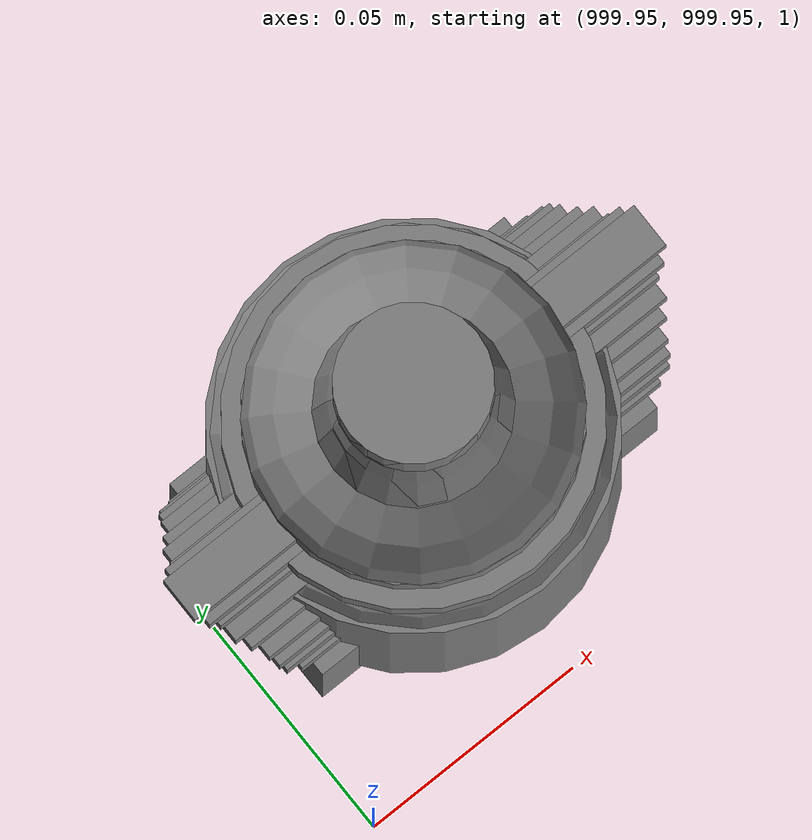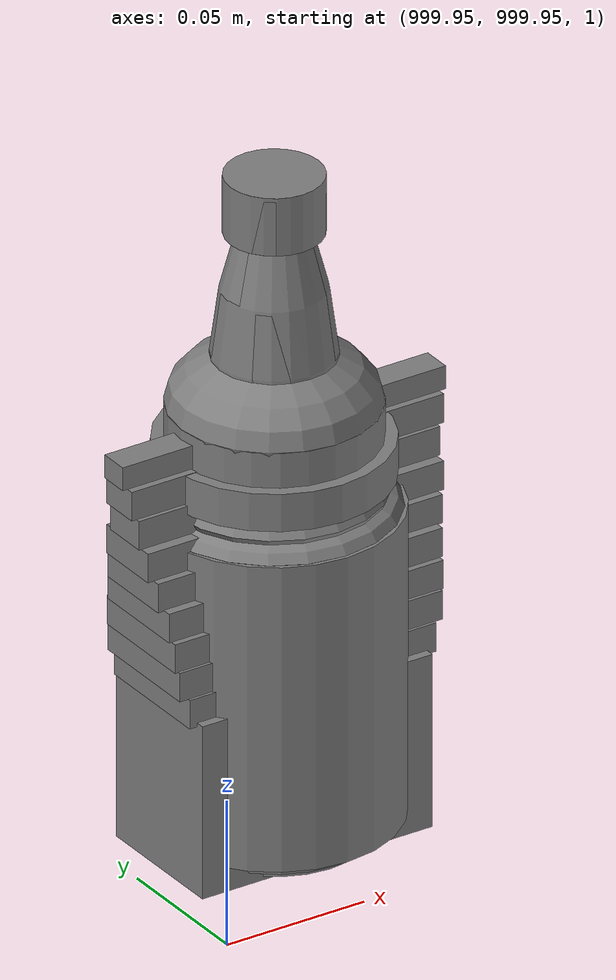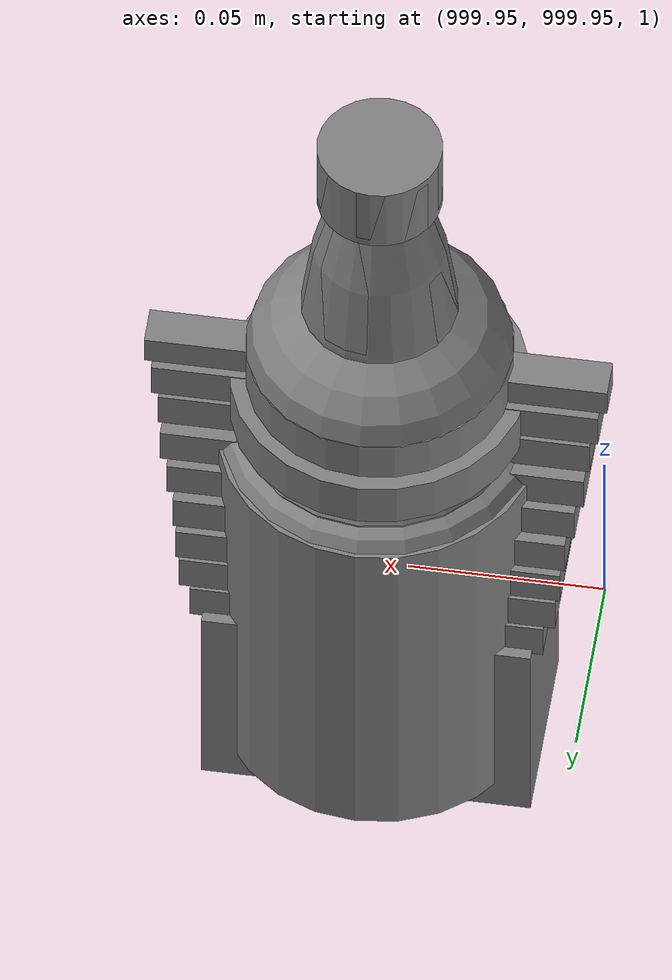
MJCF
<mujoco>
    <option gravity="0.000000000 0.000000000 -9.810000420" timestep="0.0166666" integrator="implicitfast" density="1.225" viscosity="1.8000001e-05" noslip_iterations="10" iterations="100" sdf_iterations="50">
        <flag multiccd="disable"/>
    </option>
    <size memory="1000M"/>
    <compiler coordinate="local"/>
    <worldbody>
        <light cutoff="30" pos="0 1 1" dir="0 -1 -2"/>
        <light cutoff="30" pos="0 -1 1" dir="0 1 -2"/>
        <body pos="-7.168000221 2.823999882 1.227496982" euler="-0.283413976 0.056829724 -0.133293271" name="openloong_gripper_2f85_fix_base_usda_Pos">
            <geom contype="1" conaffinity="1" density="1000" type="box" material="" rgba="0.500000000 0.500000000 0.500000000 1.000000000" solimp="0.899999976 0.949999988 0.001000000" friction="1.000000000 0.005000000 0.000100000" solref="0.020000000 1.000000000" margin="0" condim="3" group="0" pos="-0.002278805 0.074524641 -0.004134059" quat="0.315989345 0.948763072 -0.000000000 0.000000000" size="0.059999999 0.013000000 0.035000000" name="openloong_gripper_2f85_fix_base_usda_geom_69AD32AF_1F5F_4CE2_820C_D8A43957426F"/>
            <geom contype="1" conaffinity="1" density="1000" type="box" material="" rgba="0.500000000 0.500000000 0.500000000 1.000000000" solimp="0.899999976 0.949999988 0.001000000" friction="1.000000000 0.005000000 0.000100000" solref="0.020000000 1.000000000" margin="0" condim="3" group="0" pos="-0.002278805 0.078031301 0.008128285" quat="0.990447521 -0.137893379 -0.000000000 -0.000000000" size="0.059999999 0.010000000 0.035000000" name="openloong_gripper_2f85_fix_base_usda_geom_A24F466C_F99B_44D5_83E5_2CBF4AA8F0D8"/>
            <geom contype="1" conaffinity="1" density="1000" type="box" material="" rgba="0.500000000 0.500000000 0.500000000 1.000000000" solimp="0.899999976 0.949999988 0.001000000" friction="1.000000000 0.005000000 0.000100000" solref="0.020000000 1.000000000" margin="0" condim="3" group="0" pos="-0.002278805 0.080785275 -0.002596974" quat="0.287325472 -0.957833409 0.000000000 -0.000000000" size="0.059999999 0.013000000 0.035000000" name="openloong_gripper_2f85_fix_base_usda_geom_3A0C733D_EA54_4F9F_959B_6B1B1136EAA0"/>
            <geom contype="1" conaffinity="1" density="1000" type="box" material="" rgba="0.500000000 0.500000000 0.500000000 1.000000000" solimp="0.899999976 0.949999988 0.001000000" friction="1.000000000 0.005000000 0.000100000" solref="0.020000000 1.000000000" margin="0" condim="3" group="0" pos="-0.002278805 -0.098804474 -0.020146966" quat="0.988851666 0.148906454 0.000000000 -0.000000000" size="0.059999999 0.022000000 0.020000000" name="openloong_gripper_2f85_fix_base_usda_geom_9C40EFFF_63CF_4155_B5BF_FF519295902D"/>
            <geom contype="1" conaffinity="1" density="1000" type="box" material="" rgba="0.500000000 0.500000000 0.500000000 1.000000000" solimp="0.899999976 0.949999988 0.001000000" friction="1.000000000 0.005000000 0.000100000" solref="0.020000000 1.000000000" margin="0" condim="3" group="0" pos="-0.002279282 0.019920111 0.012102962" quat="0.995421767 0.095583342 -0.000000000 -0.000000000" size="0.059999999 0.025000000 0.026000001" name="openloong_gripper_2f85_fix_base_usda_geom_42513519_E467_40C8_A2E2_392D1CC461FD"/>
            <geom contype="1" conaffinity="1" density="1000" type="box" material="" rgba="0.500000000 0.500000000 0.500000000 1.000000000" solimp="0.899999976 0.949999988 0.001000000" friction="1.000000000 0.005000000 0.000100000" solref="0.020000000 1.000000000" margin="0" condim="3" group="0" pos="-0.002279282 0.005734444 -0.014276862" quat="0.999571741 -0.029275302 -0.000000000 -0.000000000" size="0.059999999 0.050000001 0.010000000" name="openloong_gripper_2f85_fix_base_usda_geom_CFCB8BD6_29ED_460F_9B09_7E17EB5358E1"/>
            <geom contype="1" conaffinity="1" density="1000" type="box" material="" rgba="0.500000000 0.500000000 0.500000000 1.000000000" solimp="0.899999976 0.949999988 0.001000000" friction="1.000000000 0.005000000 0.000100000" solref="0.020000000 1.000000000" margin="0" condim="3" group="0" pos="-0.002278805 0.079460382 0.007771969" quat="0.922590554 -0.385781586 0.000000000 -0.000000000" size="0.059999999 0.010000000 0.035000000" name="openloong_gripper_2f85_fix_base_usda_geom_54C005D0_F169_4901_9C90_F033F3AEFD8C"/>
            <geom contype="1" conaffinity="1" density="1000" type="box" material="" rgba="0.500000000 0.500000000 0.500000000 1.000000000" solimp="0.899999976 0.949999988 0.001000000" friction="1.000000000 0.005000000 0.000100000" solref="0.020000000 1.000000000" margin="0" condim="3" group="0" pos="-0.002279282 0.081384182 -0.001320124" quat="0.590483785 -0.807049930 0.000000000 -0.000000000" size="0.059999999 0.013000000 0.035000000" name="openloong_gripper_2f85_fix_base_usda_geom_5EBADC73_7F1E_4B7A_8635_58E3FA708E17"/>
            <geom contype="1" conaffinity="1" density="1000" type="box" material="" rgba="0.500000000 0.500000000 0.500000000 1.000000000" solimp="0.899999976 0.949999988 0.001000000" friction="1.000000000 0.005000000 0.000100000" solref="0.020000000 1.000000000" margin="0" condim="3" group="0" pos="-0.002278805 -0.059297800 -0.007972836" quat="0.988851666 0.148906454 0.000000000 -0.000000000" size="0.059999999 0.020000000 0.022000000" name="openloong_gripper_2f85_fix_base_usda_geom_E75A64D9_0AA2_4728_8EA8_5AA6C794DA9E"/>
            <geom contype="1" conaffinity="1" density="1000" type="box" material="" rgba="0.500000000 0.500000000 0.500000000 1.000000000" solimp="0.899999976 0.949999988 0.001000000" friction="1.000000000 0.005000000 0.000100000" solref="0.020000000 1.000000000" margin="0" condim="3" group="0" pos="-0.002278805 0.076618671 -0.004656792" quat="0.004634961 0.999989629 -0.000000000 0.000000000" size="0.059999999 0.013000000 0.035000000" name="openloong_gripper_2f85_fix_base_usda_geom_C35A54B8_E670_4063_8BC1_411C9366311C"/>
            <geom contype="1" conaffinity="1" density="1000" type="box" material="" rgba="0.500000000 0.500000000 0.500000000 1.000000000" solimp="0.899999976 0.949999988 0.001000000" friction="1.000000000 0.005000000 0.000100000" solref="0.020000000 1.000000000" margin="0" condim="3" group="0" pos="-0.002279282 -0.021952629 0.002960086" quat="0.991270423 0.131847665 -0.000000000 0.000000000" size="0.059999999 0.020000000 0.024000000" name="openloong_gripper_2f85_fix_base_usda_geom_9D663CA8_93C3_485C_A8C5_7E5A0957499B"/>
            <geom contype="1" conaffinity="1" density="1000" type="box" material="" rgba="0.500000000 0.500000000 0.500000000 1.000000000" solimp="0.899999976 0.949999988 0.001000000" friction="1.000000000 0.005000000 0.000100000" solref="0.020000000 1.000000000" margin="0" condim="3" group="0" pos="-0.002278805 0.081418991 0.002587914" quat="0.803492308 -0.595315695 0.000000000 -0.000000000" size="0.059999999 0.013000000 0.035000000" name="openloong_gripper_2f85_fix_base_usda_geom_84F91788_26D5_4298_90F1_7DB150F5F9FB"/>
            <geom contype="1" conaffinity="1" density="1000" type="box" material="" rgba="0.500000000 0.500000000 0.500000000 1.000000000" solimp="0.899999976 0.949999988 0.001000000" friction="1.000000000 0.005000000 0.000100000" solref="0.020000000 1.000000000" margin="0" condim="3" group="0" pos="-0.002278805 0.061115503 0.008545756" quat="0.999326169 0.036714450 0.000000000 -0.000000000" size="0.059999999 0.020000000 0.035000000" name="openloong_gripper_2f85_fix_base_usda_geom_DC407229_0A6D_4EFF_B10A_A64055569E94"/>
            <freejoint name="openloong_gripper_2f85_fix_base_usda_pos_scan"/>
        </body>
        <body pos="1000.000000000 1000.000000000 1.000000000" euler="0.000000000 0.000000000 0.000000000" name="openloong_gripper_2f85_fix_base_usda_salt">
            <geom contype="1" conaffinity="1" density="1000" type="box" material="" rgba="0.500000000 0.500000000 0.500000000 1.000000000" solimp="0.899999976 0.949999988 0.001000000" friction="1.000000000 0.005000000 0.000100000" solref="0.020000000 1.000000000" margin="0" condim="3" group="0" pos="0.000305176 0.000000000 0.084862232" quat="1.000000000 0.000000000 0.000000000 0.000000000" size="0.048999999 0.018999999 0.005000000" name="openloong_gripper_2f85_fix_base_usda_geom_72BE18D1_697D_4583_8163_6FF0112467A0"/>
            <geom contype="1" conaffinity="1" density="1000" type="box" material="" rgba="0.500000000 0.500000000 0.500000000 1.000000000" solimp="0.899999976 0.949999988 0.001000000" friction="1.000000000 0.005000000 0.000100000" solref="0.020000000 1.000000000" margin="0" condim="3" group="0" pos="0.000305176 0.000000000 0.104564309" quat="1.000000000 0.000000000 0.000000000 0.000000000" size="0.052000001 0.014000000 0.005000000" name="openloong_gripper_2f85_fix_base_usda_geom_494053A8_F73D_4357_B68D_8821B6764215"/>
            <geom contype="1" conaffinity="1" density="1000" type="box" material="" rgba="0.500000000 0.500000000 0.500000000 1.000000000" solimp="0.899999976 0.949999988 0.001000000" friction="1.000000000 0.005000000 0.000100000" solref="0.020000000 1.000000000" margin="0" condim="3" group="0" pos="0.000305176 0.000000000 0.114487171" quat="1.000000000 0.000000000 0.000000000 0.000000000" size="0.054000001 0.011500000 0.005000000" name="openloong_gripper_2f85_fix_base_usda_geom_B6DDFCB6_5CCF_429E_B2BB_5CB7FC7D73CA"/>
            <geom contype="1" conaffinity="1" density="1000" type="box" material="" rgba="0.500000000 0.500000000 0.500000000 1.000000000" solimp="0.899999976 0.949999988 0.001000000" friction="1.000000000 0.005000000 0.000100000" solref="0.020000000 1.000000000" margin="0" condim="3" group="0" pos="0.000305176 0.000000000 0.075103164" quat="1.000000000 0.000000000 0.000000000 0.000000000" size="0.048000000 0.020000000 0.005000000" name="openloong_gripper_2f85_fix_base_usda_geom_A57850A3_C4FB_45BC_86D7_674F24789FA2"/>
            <geom contype="1" conaffinity="1" density="1000" type="box" material="" rgba="0.500000000 0.500000000 0.500000000 1.000000000" solimp="0.899999976 0.949999988 0.001000000" friction="1.000000000 0.005000000 0.000100000" solref="0.020000000 1.000000000" margin="0" condim="3" group="0" pos="0.000305176 0.000000000 0.134892464" quat="1.000000000 0.000000000 0.000000000 0.000000000" size="0.057000000 0.007000000 0.005000000" name="openloong_gripper_2f85_fix_base_usda_geom_82A2D7B7_C489_428E_B935_3B2837CA7200"/>
            <geom contype="1" conaffinity="1" density="1000" type="box" material="" rgba="0.500000000 0.500000000 0.500000000 1.000000000" solimp="0.899999976 0.949999988 0.001000000" friction="1.000000000 0.005000000 0.000100000" solref="0.020000000 1.000000000" margin="0" condim="3" group="0" pos="0.000305176 0.000000000 0.094920278" quat="1.000000000 0.000000000 0.000000000 0.000000000" size="0.050000001 0.017000001 0.005000000" name="openloong_gripper_2f85_fix_base_usda_geom_077BDC86_9391_4BC8_8CB0_A01C9694230C"/>
            <geom contype="1" conaffinity="1" density="1000" type="box" material="" rgba="0.500000000 0.500000000 0.500000000 1.000000000" solimp="0.899999976 0.949999988 0.001000000" friction="1.000000000 0.005000000 0.000100000" solref="0.020000000 1.000000000" margin="0" condim="3" group="0" pos="0.000305176 0.000000000 0.065204859" quat="1.000000000 0.000000000 0.000000000 0.000000000" size="0.045000002 0.021000000 0.005000000" name="openloong_gripper_2f85_fix_base_usda_geom_CC7DD5C7_C69F_43F0_92CB_9B221E67F60C"/>
            <geom contype="1" conaffinity="1" density="1000" type="box" material="" rgba="0.500000000 0.500000000 0.500000000 1.000000000" solimp="0.899999976 0.949999988 0.001000000" friction="1.000000000 0.005000000 0.000100000" solref="0.020000000 1.000000000" margin="0" condim="3" group="0" pos="0.000305176 0.000000000 0.144135714" quat="1.000000000 0.000000000 0.000000000 0.000000000" size="0.059000000 0.005000000 0.004000000" name="openloong_gripper_2f85_fix_base_usda_geom_EBDA2DFD_A657_4E94_AA84_E81FC6A4B87F"/>
            <geom contype="1" conaffinity="1" density="1000" type="box" material="" rgba="0.500000000 0.500000000 0.500000000 1.000000000" solimp="0.899999976 0.949999988 0.001000000" friction="1.000000000 0.005000000 0.000100000" solref="0.020000000 1.000000000" margin="0" condim="3" group="0" pos="0.000000000 0.000000000 0.031593561" quat="1.000000000 0.000000000 0.000000000 0.000000000" size="0.041999999 0.024000000 0.029999999" name="openloong_gripper_2f85_fix_base_usda_geom_28289329_21A5_476C_A24A_2CF3E5B767A2"/>
            <geom contype="1" conaffinity="1" density="1000" type="box" material="" rgba="0.500000000 0.500000000 0.500000000 1.000000000" solimp="0.899999976 0.949999988 0.001000000" friction="1.000000000 0.005000000 0.000100000" solref="0.020000000 1.000000000" margin="0" condim="3" group="0" pos="0.000305176 0.000000000 0.124608755" quat="1.000000000 0.000000000 0.000000000 0.000000000" size="0.055000000 0.008000000 0.005000000" name="openloong_gripper_2f85_fix_base_usda_geom_521D91BD_2745_4AFE_8AA2_00A7C52041D9"/>
            <freejoint name="openloong_gripper_2f85_fix_base_usda_salt_joint"/>
            <site size="0.005000000 0.005000000 0.005000000" rgba="0.500000000 0.500000000 0.500000000 1.000000000" pos="0.000000000 0.000000000 0.000000000" quat="1.000000000 0.000000000 0.000000000 0.000000000" group="0" type="sphere" name="openloong_gripper_2f85_fix_base_usda_saltsite"/>
        </body>
        <body pos="1000.000000000 1000.000000000 1.000000000" euler="0.000000000 0.000000000 0.000000000" name="openloong_gripper_2f85_fix_base_usda_bottle_blue">
            <geom contype="1" conaffinity="1" density="1000" type="ellipsoid" material="" rgba="0.500000000 0.500000000 0.500000000 1.000000000" solimp="0.899999976 0.949999988 0.001000000" friction="1.000000000 0.005000000 0.000100000" solref="0.020000000 1.000000000" margin="0" condim="3" group="0" pos="0.000000000 0.000000000 0.118920922" quat="1.000000000 0.000000000 0.000000000 0.000000000" size="0.030999999 0.030999999 0.029999999" name="openloong_gripper_2f85_fix_base_usda_geom_49CA159E_B5BD_4E37_BAB3_7DF2452566F3"/>
            <geom contype="1" conaffinity="1" density="1000" type="box" material="" rgba="0.500000000 0.500000000 0.500000000 1.000000000" solimp="0.899999976 0.949999988 0.001000000" friction="1.000000000 0.005000000 0.000100000" solref="0.020000000 1.000000000" margin="0" condim="3" group="0" pos="0.000000000 0.000000000 0.002164602" quat="1.000000000 0.000000000 0.000000000 0.000000000" size="0.020000000 0.020000000 0.003000000" name="openloong_gripper_2f85_fix_base_usda_geom_19C81832_D21E_4C29_B770_0E426075E471"/>
            <geom contype="1" conaffinity="1" density="1000" type="cylinder" material="" rgba="0.500000000 0.500000000 0.500000000 1.000000000" solimp="0.899999976 0.949999988 0.001000000" friction="1.000000000 0.005000000 0.000100000" solref="0.020000000 1.000000000" margin="0" condim="3" group="0" pos="0.000000000 -0.000366211 0.060859680" quat="1.000000000 0.000000000 0.000000000 0.000000000" size="0.030999999 0.057999998 1.000000000" name="openloong_gripper_2f85_fix_base_usda_geom_53E8B0A1_C7AD_45DD_8067_A2F97C324BE2"/>
            <geom contype="1" conaffinity="1" density="1000" type="cylinder" material="" rgba="0.500000000 0.500000000 0.500000000 1.000000000" solimp="0.899999976 0.949999988 0.001000000" friction="1.000000000 0.005000000 0.000100000" solref="0.020000000 1.000000000" margin="0" condim="3" group="0" pos="0.000000000 0.000000000 0.220594406" quat="1.000000000 0.000000000 0.000000000 0.000000000" size="0.016000001 0.010000000 1.000000000" name="openloong_gripper_2f85_fix_base_usda_geom_827370E3_BA1D_499E_9411_B7C26B7BF461"/>
            <geom contype="1" conaffinity="1" density="1000" type="ellipsoid" material="" rgba="0.500000000 0.500000000 0.500000000 1.000000000" solimp="0.899999976 0.949999988 0.001000000" friction="1.000000000 0.005000000 0.000100000" solref="0.020000000 1.000000000" margin="0" condim="3" group="0" pos="0.000000000 0.000000000 0.144259930" quat="1.000000000 0.000000000 0.000000000 0.000000000" size="0.021000000 0.021000000 0.079999998" name="openloong_gripper_2f85_fix_base_usda_geom_2C4E1974_18CD_40E0_B8A9_F970DF7BE639"/>
            <freejoint name="openloong_gripper_2f85_fix_base_usda_bottle_blue_joint"/>
            <site size="0.005000000 0.005000000 0.005000000" rgba="0.500000000 0.500000000 0.500000000 1.000000000" pos="0.000000000 0.000000000 0.000000000" quat="0.999961913 0.008726535 0.000000000 0.000000000" group="0" type="sphere" name="openloong_gripper_2f85_fix_base_usda_bottle_bluesite"/>
        </body>
        <body pos="-2.327591419 6.558807373 1.690672398" euler="130.638305664 84.529487610 110.703552246" mocap="true" name="spotlight5_SpotLight"/>
        <body pos="1000.000000000 1000.000000000 1.000000000" euler="0.000000000 0.000000000 0.000000000" name="openloong_gripper_2f85_fix_base_usda_can">
            <geom contype="1" conaffinity="1" density="1000" type="cylinder" material="" rgba="0.500000000 0.500000000 0.500000000 1.000000000" solimp="0.899999976 0.949999988 0.001000000" friction="1.000000000 0.005000000 0.000100000" solref="0.020000000 1.000000000" margin="0" condim="3" group="0" pos="0.000000000 0.000000000 0.079676986" quat="1.000000000 0.000000000 0.000000000 0.000000000" size="0.034000002 0.071999997 1.000000000" name="openloong_gripper_2f85_fix_base_usda_geom_EDDD6A85_7C9B_46CE_9AE8_C199502E667B"/>
            <geom contype="1" conaffinity="1" density="1000" type="ellipsoid" material="" rgba="0.500000000 0.500000000 0.500000000 1.000000000" solimp="0.899999976 0.949999988 0.001000000" friction="1.000000000 0.005000000 0.000100000" solref="0.020000000 1.000000000" margin="0" condim="3" group="0" pos="0.000000000 0.000000000 0.151854277" quat="1.000000000 0.000000000 0.000000000 0.000000000" size="0.034000002 0.034000002 0.020000000" name="openloong_gripper_2f85_fix_base_usda_geom_631B0008_FAB2_4B29_A2A5_B065CA2D3ED2"/>
            <geom contype="1" conaffinity="1" density="1000" type="box" material="" rgba="0.500000000 0.500000000 0.500000000 1.000000000" solimp="0.899999976 0.949999988 0.001000000" friction="1.000000000 0.005000000 0.000100000" solref="0.020000000 1.000000000" margin="0" condim="3" group="0" pos="0.000000000 0.000000000 0.004777670" quat="1.000000000 0.000000000 0.000000000 0.000000000" size="0.020000000 0.020000000 0.005000000" name="openloong_gripper_2f85_fix_base_usda_geom_5120AAB7_C173_472B_8DCE_61F878B14ED6"/>
            <freejoint name="openloong_gripper_2f85_fix_base_usda_can_joint"/>
            <site size="0.005000000 0.005000000 0.005000000" rgba="0.500000000 0.500000000 0.500000000 1.000000000" pos="0.000000000 0.000000000 0.000000000" quat="1.000000000 0.000000000 0.000000000 0.000000000" group="0" type="sphere" name="openloong_gripper_2f85_fix_base_usda_cansite"/>
        </body>
        <body pos="1000.000000000 1000.000000000 1.000000000" euler="0.000000000 0.000000000 0.000000000" name="openloong_gripper_2f85_fix_base_usda_jar_01">
            <geom contype="1" conaffinity="1" density="1000" type="box" material="" rgba="0.500000000 0.500000000 0.500000000 1.000000000" solimp="0.899999976 0.949999988 0.001000000" friction="1.000000000 0.005000000 0.000100000" solref="0.020000000 1.000000000" margin="0" condim="3" group="0" pos="0.000000000 0.000000000 0.006158113" quat="1.000000000 0.000000000 0.000000000 0.000000000" size="0.020000000 0.020000000 0.005000000" name="openloong_gripper_2f85_fix_base_usda_geom_E7007DF6_D493_4B5F_A65B_E0A82CB7ED1B"/>
            <geom contype="1" conaffinity="1" density="1000" type="cylinder" material="" rgba="0.500000000 0.500000000 0.500000000 1.000000000" solimp="0.899999976 0.949999988 0.001000000" friction="1.000000000 0.005000000 0.000100000" solref="0.020000000 1.000000000" margin="0" condim="3" group="0" pos="0.000000000 0.000000000 0.062744498" quat="1.000000000 0.000000000 0.000000000 0.000000000" size="0.041000001 0.052999999 1.000000000" name="openloong_gripper_2f85_fix_base_usda_geom_B621C783_4FC6_4BA4_B383_5B4B74310B14"/>
            <geom contype="1" conaffinity="1" density="1000" type="ellipsoid" material="" rgba="0.500000000 0.500000000 0.500000000 1.000000000" solimp="0.899999976 0.949999988 0.001000000" friction="1.000000000 0.005000000 0.000100000" solref="0.020000000 1.000000000" margin="0" condim="3" group="0" pos="0.000000000 0.000000000 0.122252703" quat="1.000000000 0.000000000 0.000000000 0.000000000" size="0.035999998 0.035999998 0.010000000" name="openloong_gripper_2f85_fix_base_usda_geom_AB8DC40F_D2B5_4CAF_9BA7_CAF4F20FC333"/>
            <geom contype="1" conaffinity="1" density="1000" type="cylinder" material="" rgba="0.500000000 0.500000000 0.500000000 1.000000000" solimp="0.899999976 0.949999988 0.001000000" friction="1.000000000 0.005000000 0.000100000" solref="0.020000000 1.000000000" margin="0" condim="3" group="0" pos="0.000000000 0.000000000 0.015747190" quat="1.000000000 0.000000000 0.000000000 0.000000000" size="0.035000000 0.010000000 1.000000000" name="openloong_gripper_2f85_fix_base_usda_geom_AD7154C8_F18A_4D0E_95EB_0E41D32FCCBC"/>
            <geom contype="1" conaffinity="1" density="1000" type="ellipsoid" material="" rgba="0.500000000 0.500000000 0.500000000 1.000000000" solimp="0.899999976 0.949999988 0.001000000" friction="1.000000000 0.005000000 0.000100000" solref="0.020000000 1.000000000" margin="0" condim="3" group="0" pos="0.000000000 0.000000000 0.115815401" quat="1.000000000 0.000000000 0.000000000 0.000000000" size="0.039999999 0.039999999 0.010000000" name="openloong_gripper_2f85_fix_base_usda_geom_0FA8094E_4A1D_4410_B182_DBACBDC32E63"/>
            <geom contype="1" conaffinity="1" density="1000" type="cylinder" material="" rgba="0.500000000 0.500000000 0.500000000 1.000000000" solimp="0.899999976 0.949999988 0.001000000" friction="1.000000000 0.005000000 0.000100000" solref="0.020000000 1.000000000" margin="0" condim="3" group="0" pos="0.000000000 0.000000000 0.133183479" quat="1.000000000 0.000000000 0.000000000 0.000000000" size="0.037999999 0.006500000 1.000000000" name="openloong_gripper_2f85_fix_base_usda_geom_DB70ED1E_4921_43A3_80FC_D86F1E2CA43D"/>
            <freejoint name="openloong_gripper_2f85_fix_base_usda_jar_01_joint"/>
            <site size="0.005000000 0.005000000 0.005000000" rgba="0.500000000 0.500000000 0.500000000 1.000000000" pos="0.000000000 0.000000000 0.000000000" quat="1.000000000 0.000000000 0.000000000 0.000000000" group="0" type="sphere" name="openloong_gripper_2f85_fix_base_usda_jar_01site"/>
        </body>
        <body pos="-2.224244356 6.294197559 1.842940450" euler="9.340506554 57.312149048 81.694374084" mocap="true" name="spotlight3_SpotLight"/>
        <body pos="1000.000000000 1000.000000000 1.000000000" euler="0.000000000 0.000000000 0.000000000" name="openloong_gripper_2f85_fix_base_usda_bottle_red">
            <geom contype="1" conaffinity="1" density="1000" type="ellipsoid" material="" rgba="0.500000000 0.500000000 0.500000000 1.000000000" solimp="0.899999976 0.949999988 0.001000000" friction="1.000000000 0.005000000 0.000100000" solref="0.020000000 1.000000000" margin="0" condim="3" group="0" pos="0.000000000 0.000000000 0.144284487" quat="1.000000000 0.000000000 0.000000000 0.000000000" size="0.021000000 0.021000000 0.079999998" name="openloong_gripper_2f85_fix_base_usda_geom_F2A68C99_D61A_4142_ABE2_8FB646DA2154"/>
            <geom contype="1" conaffinity="1" density="1000" type="cylinder" material="" rgba="0.500000000 0.500000000 0.500000000 1.000000000" solimp="0.899999976 0.949999988 0.001000000" friction="1.000000000 0.005000000 0.000100000" solref="0.020000000 1.000000000" margin="0" condim="3" group="0" pos="0.000000000 0.000000000 0.220618963" quat="1.000000000 0.000000000 0.000000000 0.000000000" size="0.016000001 0.010000000 1.000000000" name="openloong_gripper_2f85_fix_base_usda_geom_777943CB_242E_4477_8739_1DD5D77E3F07"/>
            <geom contype="1" conaffinity="1" density="1000" type="ellipsoid" material="" rgba="0.500000000 0.500000000 0.500000000 1.000000000" solimp="0.899999976 0.949999988 0.001000000" friction="1.000000000 0.005000000 0.000100000" solref="0.020000000 1.000000000" margin="0" condim="3" group="0" pos="0.000000000 0.000000000 0.118945479" quat="1.000000000 0.000000000 0.000000000 0.000000000" size="0.030999999 0.030999999 0.029999999" name="openloong_gripper_2f85_fix_base_usda_geom_FBAB8527_AC90_4276_84B8_0761C2EFE610"/>
            <geom contype="1" conaffinity="1" density="1000" type="box" material="" rgba="0.500000000 0.500000000 0.500000000 1.000000000" solimp="0.899999976 0.949999988 0.001000000" friction="1.000000000 0.005000000 0.000100000" solref="0.020000000 1.000000000" margin="0" condim="3" group="0" pos="0.000000000 0.000000000 0.002189159" quat="1.000000000 0.000000000 0.000000000 0.000000000" size="0.020000000 0.020000000 0.003000000" name="openloong_gripper_2f85_fix_base_usda_geom_A2507CE0_F6E7_45A2_A208_BFE5C58055AD"/>
            <geom contype="1" conaffinity="1" density="1000" type="cylinder" material="" rgba="0.500000000 0.500000000 0.500000000 1.000000000" solimp="0.899999976 0.949999988 0.001000000" friction="1.000000000 0.005000000 0.000100000" solref="0.020000000 1.000000000" margin="0" condim="3" group="0" pos="0.000000000 -0.000366211 0.060884237" quat="1.000000000 0.000000000 0.000000000 0.000000000" size="0.030999999 0.057999998 1.000000000" name="openloong_gripper_2f85_fix_base_usda_geom_EBC8B658_9F3C_42B9_AA20_66ECD2C7B9F2"/>
            <freejoint name="openloong_gripper_2f85_fix_base_usda_bottle_red_joint"/>
            <site size="0.005000000 0.005000000 0.005000000" rgba="0.500000000 0.500000000 0.500000000 1.000000000" pos="0.000000000 0.000000000 0.000000000" quat="0.999961913 0.008726535 0.000000000 0.000000000" group="0" type="sphere" name="openloong_gripper_2f85_fix_base_usda_bottle_redsite"/>
        </body>
        <body pos="-2.263298750 5.869570255 1.804352283" euler="0.969198108 -37.635314941 121.373138428" mocap="true" name="spotlight1_SpotLight"/>
        <body pos="0.000000000 0.000000000 0.000000000" euler="0.000000000 0.000000000 0.000000000" name="Interactive Objects_Interactive Objects"/>
        <body pos="0.000000000 0.000000000 0.000000000" euler="0.000000000 0.000000000 0.000000000" name=" Static Objects_ Static Objects">
            <geom contype="1" conaffinity="1" density="1000" type="box" material="" rgba="0.500000000 0.500000000 0.500000000 1.000000000" solimp="0.899999976 0.949999988 0.001000000" friction="1.000000000 0.005000000 0.000100000" solref="0.020000000 1.000000000" margin="0" condim="3" group="0" pos="-6.286010742 6.153595448 1.563861728" quat="0.707107067 0.000000000 0.000000000 0.707106471" size="0.529999971 3.134999990 0.025000000" name=" Static Objects_geom_8D7F5CEA_00DD_4C44_AC8A_A0C824E49A12"/>
            <geom contype="1" conaffinity="1" density="1000" type="box" material="" rgba="0.500000000 0.500000000 0.500000000 1.000000000" solimp="0.899999976 0.949999988 0.001000000" friction="1.000000000 0.005000000 0.000100000" solref="0.020000000 1.000000000" margin="0" condim="3" group="0" pos="-3.101639986 6.150595188 1.018643856" quat="1.000000000 0.000000000 0.000000000 0.000000000" size="0.050000001 0.579999983 1.019999981" name=" Static Objects_geom_79F32308_368A_4514_BB21_027A555477CA"/>
            <geom contype="1" conaffinity="1" density="1000" type="box" material="" rgba="0.500000000 0.500000000 0.500000000 1.000000000" solimp="0.899999976 0.949999988 0.001000000" friction="1.000000000 0.005000000 0.000100000" solref="0.020000000 1.000000000" margin="0" condim="3" group="0" pos="-2.825197220 6.153595448 1.563861728" quat="0.707107067 0.000000000 0.000000000 0.707106471" size="0.550000012 0.239999995 0.025000000" name=" Static Objects_geom_78D6BD44_626D_45D8_9D3C_976A92B7EC2D"/>
            <geom contype="1" conaffinity="1" density="1000" type="box" material="" rgba="0.500000000 0.500000000 0.500000000 1.000000000" solimp="0.899999976 0.949999988 0.001000000" friction="1.000000000 0.005000000 0.000100000" solref="0.020000000 1.000000000" margin="0" condim="3" group="0" pos="-6.311686516 6.153595448 1.018643856" quat="0.707107067 0.000000000 0.000000000 0.707106471" size="0.050000001 3.150000095 1.019999981" name=" Static Objects_geom_E9CFC24C_C1E1_45C7_8500_49F96E7E4C8C"/>
            <geom contype="1" conaffinity="1" density="1000" type="box" material="" rgba="0.500000000 0.500000000 0.500000000 1.000000000" solimp="0.899999976 0.949999988 0.001000000" friction="1.000000000 0.005000000 0.000100000" solref="0.020000000 1.000000000" margin="0" condim="3" group="0" pos="-2.825197220 6.153595448 1.115278244" quat="0.707107067 0.000000000 0.000000000 0.707106471" size="0.550000012 0.239999995 0.025000000" name=" Static Objects_geom_35E92E04_67CD_45BB_A5FE_41910D3A1161"/>
            <geom contype="1" conaffinity="1" density="1000" type="box" material="" rgba="0.500000000 0.500000000 0.500000000 1.000000000" solimp="0.899999976 0.949999988 0.001000000" friction="1.000000000 0.005000000 0.000100000" solref="0.020000000 1.000000000" margin="0" condim="3" group="0" pos="-6.293097973 6.153595448 1.114443064" quat="0.707107067 0.000000000 0.000000000 0.707106471" size="0.529999971 3.134999990 0.025000000" name=" Static Objects_geom_F239B3BD_AE38_4CDF_ACF6_F07A29E1336C"/>
            <geom contype="1" conaffinity="1" density="1000" type="box" material="" rgba="0.500000000 0.500000000 0.500000000 1.000000000" solimp="0.899999976 0.949999988 0.001000000" friction="1.000000000 0.005000000 0.000100000" solref="0.020000000 1.000000000" margin="0" condim="3" group="0" pos="-2.825197220 6.153595448 0.629031777" quat="0.707107067 0.000000000 0.000000000 0.707106471" size="0.550000012 0.239999995 0.025000000" name=" Static Objects_geom_3C2B87DC_BB08_4025_AC45_52170313C6D9"/>
            <geom contype="1" conaffinity="1" density="1000" type="box" material="" rgba="0.500000000 0.500000000 0.500000000 1.000000000" solimp="0.899999976 0.949999988 0.001000000" friction="1.000000000 0.005000000 0.000100000" solref="0.020000000 1.000000000" margin="0" condim="3" group="0" pos="-6.286010742 6.153595448 0.096129179" quat="0.707107067 0.000000000 0.000000000 0.707106471" size="0.529999971 3.134999990 0.098999999" name=" Static Objects_geom_B8860954_897E_404F_995A_4B41716DE7EE"/>
            <geom contype="1" conaffinity="1" density="1000" type="box" material="" rgba="0.500000000 0.500000000 0.500000000 1.000000000" solimp="0.899999976 0.949999988 0.001000000" friction="1.000000000 0.005000000 0.000100000" solref="0.020000000 1.000000000" margin="0" condim="3" group="0" pos="-2.825197220 6.153595448 0.097434282" quat="0.707107067 0.000000000 0.000000000 0.707106471" size="0.550000012 0.239999995 0.098999999" name=" Static Objects_geom_4BBD1042_A27C_4F1C_A1E8_E190D6C83463"/>
            <geom contype="1" conaffinity="1" density="1000" type="box" material="" rgba="0.500000000 0.500000000 0.500000000 1.000000000" solimp="0.899999976 0.949999988 0.001000000" friction="1.000000000 0.005000000 0.000100000" solref="0.020000000 1.000000000" margin="0" condim="3" group="0" pos="-6.286010742 6.153595448 0.629031777" quat="0.707107067 0.000000000 0.000000000 0.707106471" size="0.529999971 3.134999990 0.025000000" name=" Static Objects_geom_889203D8_E311_4BE2_AC75_9AB0878F3E54"/>
            <geom contype="1" conaffinity="1" density="1000" type="box" material="" rgba="0.500000000 0.500000000 0.500000000 1.000000000" solimp="0.899999976 0.949999988 0.001000000" friction="1.000000000 0.005000000 0.000100000" solref="0.020000000 1.000000000" margin="0" condim="3" group="0" pos="-6.000000000 20.159999847 2.000000000" quat="1.000000000 0.000000000 0.000000000 0.000000000" size="6.079999924 0.070000000 2.000000000" name=" Static Objects_geom_55FEF0B8_84B3_4101_81DE_6CB678A5AF67"/>
            <geom contype="1" conaffinity="1" density="1000" type="box" material="" rgba="0.500000000 0.500000000 0.500000000 1.000000000" solimp="0.899999976 0.949999988 0.001000000" friction="1.000000000 0.005000000 0.000100000" solref="0.020000000 1.000000000" margin="0" condim="3" group="0" pos="-6.000000000 0.035000000 2.000000000" quat="1.000000000 0.000000000 0.000000000 0.000000000" size="6.079999924 0.070000000 2.000000000" name=" Static Objects_geom_CA9B8BA5_3E1F_4505_83C9_49C503A92A57"/>
            <geom contype="1" conaffinity="1" density="1000" type="box" material="" rgba="0.500000000 0.500000000 0.500000000 1.000000000" solimp="0.899999976 0.949999988 0.001000000" friction="1.000000000 0.005000000 0.000100000" solref="0.020000000 1.000000000" margin="0" condim="3" group="0" pos="0.000000000 10.000000000 2.000000000" quat="1.000000000 0.000000000 0.000000000 0.000000000" size="0.070000000 10.500000000 2.000000000" name=" Static Objects_geom_88D1A96B_D8D5_4F84_A4F9_382C35F941FA"/>
            <geom contype="1" conaffinity="1" density="1000" type="box" material="" rgba="0.500000000 0.500000000 0.500000000 1.000000000" solimp="0.899999976 0.949999988 0.001000000" friction="1.000000000 0.005000000 0.000100000" solref="0.020000000 1.000000000" margin="0" condim="3" group="0" pos="-12.050000191 10.000000000 2.000000000" quat="1.000000000 0.000000000 0.000000000 0.000000000" size="0.070000000 10.500000000 2.000000000" name=" Static Objects_geom_EE8B0071_E3B7_4DC8_A065_6C299A6043B7"/>
            <geom contype="1" conaffinity="1" density="1000" type="plane" material="" rgba="0.500000000 0.500000000 0.500000000 1.000000000" solimp="0.899999976 0.949999988 0.001000000" friction="1.000000000 0.005000000 0.000100000" solref="0.020000000 1.000000000" margin="0" condim="3" group="0" pos="-6.000000000 10.399999619 0.000000000" quat="1.000000000 0.000000000 0.000000000 0.000000000" size="6.050000191 10.800000191 0.010000000" name=" Static Objects_geom_011265DB_388F_4702_B873_6FABB7565945"/>
            <geom contype="1" conaffinity="1" density="1000" type="box" material="" rgba="0.500000000 0.500000000 0.500000000 1.000000000" solimp="0.899999976 0.949999988 0.001000000" friction="1.000000000 0.005000000 0.000100000" solref="0.020000000 1.000000000" margin="0" condim="3" group="0" pos="-8.830721855 2.096410990 0.549305558" quat="1.000000000 0.000000000 0.000000000 0.000000000" size="0.280000001 0.430000007 0.550000012" name=" Static Objects_geom_38729E5D_A80F_4A63_B849_1DD6411A86DD"/>
            <geom contype="1" conaffinity="1" density="1000" type="box" material="" rgba="0.500000000 0.500000000 0.500000000 1.000000000" solimp="0.899999976 0.949999988 0.001000000" friction="1.000000000 0.005000000 0.000100000" solref="0.020000000 1.000000000" margin="0" condim="3" group="0" pos="-6.460197449 2.937205315 0.548931718" quat="1.000000000 0.000000000 0.000000000 0.000000000" size="2.650000095 0.430000007 0.550000012" name=" Static Objects_geom_BD6E4EB9_526A_4ECF_B20C_C0CD8F349D5D"/>
            <geom contype="1" conaffinity="1" density="1000" type="box" material="" rgba="0.500000000 0.500000000 0.500000000 1.000000000" solimp="0.899999976 0.949999988 0.001000000" friction="1.000000000 0.005000000 0.000100000" solref="0.020000000 1.000000000" margin="0" condim="3" group="0" pos="-4.240264893 1.327049494 0.549888909" quat="1.000000000 0.000000000 0.000000000 0.000000000" size="0.430000007 1.200000048 0.550000012" name=" Static Objects_geom_3423ACE0_C209_4184_BD5E_7FFF672F9CE3"/>
            <geom contype="1" conaffinity="1" density="1000" type="box" material="" rgba="0.500000000 0.500000000 0.500000000 1.000000000" solimp="0.899999976 0.949999988 0.001000000" friction="1.000000000 0.005000000 0.000100000" solref="0.020000000 1.000000000" margin="0" condim="3" group="0" pos="-7.408766270 3.088089943 1.776644945" quat="0.928051054 0.000000000 0.000000000 0.372453064" size="0.050000001 0.100000001 0.050000001" name=" Static Objects_geom_49BCC76D_C338_4127_B075_E66953D620CF"/>
            <geom contype="1" conaffinity="1" density="1000" type="box" material="" rgba="0.500000000 0.500000000 0.500000000 1.000000000" solimp="0.899999976 0.949999988 0.001000000" friction="1.000000000 0.005000000 0.000100000" solref="0.020000000 1.000000000" margin="0" condim="3" group="0" pos="-7.437745571 3.067511320 1.289965630" quat="1.000000000 0.000000000 0.000000000 0.000000000" size="0.029999999 0.020000000 0.020000000" name=" Static Objects_geom_2C344F5B_3E31_49E1_8F0C_FDFB90DFE263"/>
            <geom contype="1" conaffinity="1" density="1000" type="box" material="" rgba="0.500000000 0.500000000 0.500000000 1.000000000" solimp="0.899999976 0.949999988 0.001000000" friction="1.000000000 0.005000000 0.000100000" solref="0.020000000 1.000000000" margin="0" condim="3" group="0" pos="-7.719123363 2.867671013 1.173410416" quat="1.000000000 0.000000000 0.000000000 0.000000000" size="0.250000000 0.250000000 0.079999998" name=" Static Objects_geom_DEF75AF1_8F58_493F_93EB_DA2B2F068DB6"/>
            <geom contype="1" conaffinity="1" density="1000" type="box" material="" rgba="0.500000000 0.500000000 0.500000000 1.000000000" solimp="0.899999976 0.949999988 0.001000000" friction="1.000000000 0.005000000 0.000100000" solref="0.020000000 1.000000000" margin="0" condim="3" group="0" pos="-7.719123363 2.958004713 1.530241251" quat="1.000000000 0.000000000 0.000000000 0.000000000" size="0.250000000 0.159999996 0.280000001" name=" Static Objects_geom_559D6FD6_CE50_4EF7_BB37_1073B1048C74"/>
            <geom contype="1" conaffinity="1" density="1000" type="cylinder" material="" rgba="0.500000000 0.500000000 0.500000000 1.000000000" solimp="0.899999976 0.949999988 0.001000000" friction="1.000000000 0.005000000 0.000100000" solref="0.020000000 1.000000000" margin="0" condim="3" group="0" pos="-7.427312374 3.069516420 1.502544641" quat="0.928051054 0.000000000 0.000000000 0.372453064" size="0.015000000 0.230000004 0.100000001" name=" Static Objects_geom_52106026_BED1_40E4_A7B5_B9D284865DC5"/>
            <geom contype="1" conaffinity="1" density="1000" type="box" material="" rgba="0.500000000 0.500000000 0.500000000 1.000000000" solimp="0.899999976 0.949999988 0.001000000" friction="1.000000000 0.005000000 0.000100000" solref="0.020000000 1.000000000" margin="0" condim="3" group="0" pos="-9.058088303 6.434794426 1.209077358" quat="1.000000000 0.000000000 0.000000000 0.000000000" size="0.250000000 0.100000001 0.070000000" name=" Static Objects_geom_355C392C_A05D_4D7D_B047_6A46D1B21922"/>
            <geom contype="1" conaffinity="1" density="1000" type="box" material="" rgba="0.500000000 0.500000000 0.500000000 1.000000000" solimp="0.899999976 0.949999988 0.001000000" friction="1.000000000 0.005000000 0.000100000" solref="0.020000000 1.000000000" margin="0" condim="3" group="0" pos="-5.611940861 6.318420410 0.350975692" quat="1.000000000 0.000000000 0.000000000 0.000000000" size="0.699999988 0.100000001 0.150000006" name=" Static Objects_geom_E083C85D_495A_426B_8E76_BD446F48F269"/>
            <geom contype="1" conaffinity="1" density="1000" type="box" material="" rgba="0.500000000 0.500000000 0.500000000 1.000000000" solimp="0.899999976 0.949999988 0.001000000" friction="1.000000000 0.005000000 0.000100000" solref="0.020000000 1.000000000" margin="0" condim="3" group="0" pos="-9.237723351 6.464855671 1.209077358" quat="1.000000000 0.000000000 0.000000000 0.000000000" size="0.100000001 0.100000001 0.070000000" name=" Static Objects_geom_C755A2EF_75B7_4D91_9431_76F58929CA99"/>
            <geom contype="1" conaffinity="1" density="1000" type="box" material="" rgba="0.500000000 0.500000000 0.500000000 1.000000000" solimp="0.899999976 0.949999988 0.001000000" friction="1.000000000 0.005000000 0.000100000" solref="0.020000000 1.000000000" margin="0" condim="3" group="0" pos="-6.300771236 6.459744930 1.744376063" quat="1.000000000 0.000000000 0.000000000 0.000000000" size="3.000000000 0.200000003 0.150000006" name=" Static Objects_geom_5A85BDD0_067C_4D96_AFD3_3E8C78CFA2F3"/>
            <geom contype="1" conaffinity="1" density="1000" type="box" material="" rgba="0.500000000 0.500000000 0.500000000 1.000000000" solimp="0.899999976 0.949999988 0.001000000" friction="1.000000000 0.005000000 0.000100000" solref="0.020000000 1.000000000" margin="0" condim="3" group="0" pos="-7.373087406 6.458900928 1.214329123" quat="1.000000000 0.000000000 0.000000000 0.000000000" size="0.250000000 0.200000003 0.075000003" name=" Static Objects_geom_0B7D04FB_735B_4AB6_AFEB_F5B078FB47CA"/>
            <geom contype="1" conaffinity="1" density="1000" type="box" material="" rgba="0.500000000 0.500000000 0.500000000 1.000000000" solimp="0.899999976 0.949999988 0.001000000" friction="1.000000000 0.005000000 0.000100000" solref="0.020000000 1.000000000" margin="0" condim="3" group="0" pos="-4.035642624 6.459744930 0.352518857" quat="1.000000000 0.000000000 0.000000000 0.000000000" size="0.800000012 0.200000003 0.150000006" name=" Static Objects_geom_67409F79_6813_4588_BC3B_02B9B2B60B5A"/>
            <geom contype="1" conaffinity="1" density="1000" type="box" material="" rgba="0.500000000 0.500000000 0.500000000 1.000000000" solimp="0.899999976 0.949999988 0.001000000" friction="1.000000000 0.005000000 0.000100000" solref="0.020000000 1.000000000" margin="0" condim="3" group="0" pos="-3.907610416 6.318625927 0.800981164" quat="1.000000000 0.000000000 0.000000000 0.000000000" size="0.500000000 0.100000001 0.150000006" name=" Static Objects_geom_62B6B6D2_A4A2_4EDF_BF9A_EE73023CA654"/>
            <geom contype="1" conaffinity="1" density="1000" type="box" material="" rgba="0.500000000 0.500000000 0.500000000 1.000000000" solimp="0.899999976 0.949999988 0.001000000" friction="1.000000000 0.005000000 0.000100000" solref="0.020000000 1.000000000" margin="0" condim="3" group="0" pos="-6.098561764 6.327973843 1.292199373" quat="1.000000000 0.000000000 0.000000000 0.000000000" size="0.500000000 0.100000001 0.150000006" name=" Static Objects_geom_C5E19CC4_F523_4983_9A08_E6D379D9AFD6"/>
            <geom contype="1" conaffinity="1" density="1000" type="box" material="" rgba="0.500000000 0.500000000 0.500000000 1.000000000" solimp="0.899999976 0.949999988 0.001000000" friction="1.000000000 0.005000000 0.000100000" solref="0.020000000 1.000000000" margin="0" condim="3" group="0" pos="-7.886891365 6.459744930 0.352518857" quat="1.000000000 0.000000000 0.000000000 0.000000000" size="1.500000000 0.200000003 0.150000006" name=" Static Objects_geom_F22BC86F_7995_432E_9C8A_0E23BEF6A6CB"/>
            <geom contype="1" conaffinity="1" density="1000" type="box" material="" rgba="0.500000000 0.500000000 0.500000000 1.000000000" solimp="0.899999976 0.949999988 0.001000000" friction="1.000000000 0.005000000 0.000100000" solref="0.020000000 1.000000000" margin="0" condim="3" group="0" pos="-6.824534416 6.447464466 1.212718010" quat="1.000000000 0.000000000 0.000000000 0.000000000" size="0.100000001 0.100000001 0.075000003" name=" Static Objects_geom_16330B84_E21A_41BB_92D0_297F4B3C3EF8"/>
            <geom contype="1" conaffinity="1" density="1000" type="box" material="" rgba="0.500000000 0.500000000 0.500000000 1.000000000" solimp="0.899999976 0.949999988 0.001000000" friction="1.000000000 0.005000000 0.000100000" solref="0.020000000 1.000000000" margin="0" condim="3" group="0" pos="-4.407354832 6.459744930 1.292199373" quat="1.000000000 0.000000000 0.000000000 0.000000000" size="1.240000010 0.200000003 0.150000006" name=" Static Objects_geom_B0CA132A_F1A8_46D8_8763_E2A411004724"/>
            <geom contype="1" conaffinity="1" density="1000" type="box" material="" rgba="0.500000000 0.500000000 0.500000000 1.000000000" solimp="0.899999976 0.949999988 0.001000000" friction="1.000000000 0.005000000 0.000100000" solref="0.020000000 1.000000000" margin="0" condim="3" group="0" pos="-6.751636982 6.459744930 0.800981164" quat="1.000000000 0.000000000 0.000000000 0.000000000" size="2.200000048 0.200000003 0.150000006" name=" Static Objects_geom_32CC7366_3BC2_435E_B383_179CB3842765"/>
            <geom contype="1" conaffinity="1" density="1000" type="box" material="" rgba="0.500000000 0.500000000 0.500000000 1.000000000" solimp="0.899999976 0.949999988 0.001000000" friction="1.000000000 0.005000000 0.000100000" solref="0.020000000 1.000000000" margin="0" condim="3" group="0" pos="-6.924745083 6.362090111 1.214329123" quat="1.000000000 0.000000000 0.000000000 0.000000000" size="0.200000003 0.100000001 0.075000003" name=" Static Objects_geom_C60E584D_C9BC_4BCF_9930_0D83BD7B03F4"/>
            <geom contype="1" conaffinity="1" density="1000" type="box" material="" rgba="0.500000000 0.500000000 0.500000000 1.000000000" solimp="0.899999976 0.949999988 0.001000000" friction="1.000000000 0.005000000 0.000100000" solref="0.020000000 1.000000000" margin="0" condim="3" group="0" pos="-8.844120979 6.464855671 1.209077358" quat="1.000000000 0.000000000 0.000000000 0.000000000" size="0.100000001 0.100000001 0.070000000" name=" Static Objects_geom_C3FB4935_026E_4166_9285_43FAA5CD7286"/>
            <geom contype="1" conaffinity="1" density="1000" type="box" material="" rgba="0.500000000 0.500000000 0.500000000 1.000000000" solimp="0.899999976 0.949999988 0.001000000" friction="1.000000000 0.005000000 0.000100000" solref="0.020000000 1.000000000" margin="0" condim="3" group="0" pos="-3.157672644 6.136868477 1.348373055" quat="1.000000000 0.000000000 0.000000000 0.000000000" size="0.200000003 0.519999981 0.300000012" name=" Static Objects_geom_A933EBFF_A70A_4E75_BD30_4CE6114FBB04"/>
        </body>
        <body pos="-6.332345009 2.779978037 1.034067392" euler="0.000000000 0.000000000 0.000000000" name="openloong_gripper_2f85_fix_base_usda_basket">
            <geom contype="1" conaffinity="1" density="100000" type="box" material="" rgba="0.500000000 0.500000000 0.500000000 1.000000000" solimp="0.899999976 0.949999988 0.001000000" friction="1.000000000 0.899999976 0.000100000" solref="0.020000000 1.000000000" margin="0" condim="3" group="0" pos="-0.039724827 -0.188568115 0.167089701" quat="0.997537494 0.070135131 0.000000000 0.000000000" size="0.150000006 0.006000000 0.108000003" name="openloong_gripper_2f85_fix_base_usda_geom_F3622721_6712_4010_91A5_BFFD11F603FD"/>
            <geom contype="1" conaffinity="1" density="100000" type="box" material="" rgba="0.500000000 0.500000000 0.500000000 1.000000000" solimp="0.899999976 0.949999988 0.001000000" friction="1.000000000 0.899999976 0.000100000" solref="0.020000000 1.000000000" margin="0" condim="3" group="0" pos="0.094372749 0.000000000 0.168361664" quat="0.706172049 0.036353335 0.036353379 0.706171215" size="0.200000003 0.006000000 0.108000003" name="openloong_gripper_2f85_fix_base_usda_geom_22704617_CBEC_49F6_888B_6FFDD968B242"/>
            <geom contype="1" conaffinity="1" density="100000" type="box" material="" rgba="0.500000000 0.500000000 0.500000000 1.000000000" solimp="0.899999976 0.949999988 0.001000000" friction="1.000000000 0.899999976 0.000100000" solref="0.020000000 1.000000000" margin="0" condim="3" group="0" pos="-0.039724827 0.000000000 0.068126202" quat="1.000000000 0.000000000 0.000000000 0.000000000" size="0.129999995 0.174999997 0.006000000" name="openloong_gripper_2f85_fix_base_usda_geom_4C1821E9_D6BD_4B98_96CE_CE6F2AD15F2F"/>
            <geom contype="1" conaffinity="1" density="100000" type="box" material="" rgba="0.500000000 0.500000000 0.500000000 1.000000000" solimp="0.899999976 0.949999988 0.001000000" friction="1.000000000 0.899999976 0.000100000" solref="0.020000000 1.000000000" margin="0" condim="3" group="0" pos="-0.039724827 0.188377380 0.167089701" quat="0.997489929 -0.070808925 0.000000000 0.000000000" size="0.150000006 0.006000000 0.108000003" name="openloong_gripper_2f85_fix_base_usda_geom_B27E952F_EB29_459B_9328_934A25C2798D"/>
            <geom contype="1" conaffinity="1" density="100000" type="box" material="" rgba="0.500000000 0.500000000 0.500000000 1.000000000" solimp="0.899999976 0.949999988 0.001000000" friction="1.000000000 0.899999976 0.000100000" solref="0.020000000 1.000000000" margin="0" condim="3" group="0" pos="-0.172339439 0.000000000 0.168361664" quat="0.706172407 -0.036353018 -0.036353093 0.706170976" size="0.200000003 0.006000000 0.108000003" name="openloong_gripper_2f85_fix_base_usda_geom_98A25498_FCD4_4E74_B28C_A71B19983465"/>
            <freejoint name="openloong_gripper_2f85_fix_base_usda_basket_joint"/>
            <site size="0.005000000 0.005000000 0.005000000" rgba="0.500000000 0.500000000 0.500000000 1.000000000" pos="0.000000000 0.000000000 0.000000000" quat="1.000000000 0.000000000 0.000000000 0.000000000" group="0" type="sphere" name="openloong_gripper_2f85_fix_base_usda_basketsite"/>
        </body>
        <body pos="-3.510578632 3.403555870 -0.000000100" euler="0.000000000 0.000000000 40.200675964" name="openloong_gripper_2f85_fix_base_usda_PZ">
            <geom contype="1" conaffinity="1" density="1000" type="box" material="" rgba="0.500000000 0.500000000 0.500000000 1.000000000" solimp="0.899999976 0.949999988 0.001000000" friction="1.000000000 0.005000000 0.000100000" solref="0.020000000 1.000000000" margin="0" condim="3" group="0" pos="-0.047453165 0.056484699 0.373715430" quat="0.934750080 0.077914521 0.028795123 0.345459938" size="0.180000007 0.010000000 0.379999995" name="openloong_gripper_2f85_fix_base_usda_geom_ECDDAE3C_F366_4090_A879_ECB6EC6B9CFD"/>
            <geom contype="1" conaffinity="1" density="1000" type="box" material="" rgba="0.500000000 0.500000000 0.500000000 1.000000000" solimp="0.899999976 0.949999988 0.001000000" friction="1.000000000 0.005000000 0.000100000" solref="0.020000000 1.000000000" margin="0" condim="3" group="0" pos="0.047452450 -0.054376602 0.374072611" quat="0.934387863 -0.082143910 -0.030358355 0.345326364" size="0.180000007 0.010000000 0.379999995" name="openloong_gripper_2f85_fix_base_usda_geom_ACBB2981_2DC1_4CA1_BC46_89BE73CB066F"/>
            <freejoint name="openloong_gripper_2f85_fix_base_usda_PZ"/>
        </body>
        <body pos="-2.436573029 6.404376507 0.137849092" euler="0.000000000 0.000000000 0.000000000" name="openloong_gripper_2f85_fix_base_usda_shoppingtrolley_01">
            <geom contype="1" conaffinity="1" density="1000" type="box" material="" rgba="0.500000000 0.500000000 0.500000000 1.000000000" solimp="0.899999976 0.949999988 0.001000000" friction="1.000000000 0.005000000 0.000100000" solref="0.020000000 1.000000000" margin="0" condim="3" group="0" pos="-0.107458733 0.238907143 0.911498845" quat="0.634576976 0.622505128 -0.330067992 -0.317575932" size="0.017999999 0.022499999 0.035999998" name="openloong_gripper_2f85_fix_base_usda_geom_5C8A4955_03AA_4829_96EE_4930E373D802"/>
            <geom contype="1" conaffinity="1" density="1000" type="box" material="" rgba="0.500000000 0.500000000 0.500000000 1.000000000" solimp="0.899999976 0.949999988 0.001000000" friction="1.000000000 0.005000000 0.000100000" solref="0.020000000 1.000000000" margin="0" condim="3" group="0" pos="-0.126757339 -0.182533979 0.598989725" quat="0.996607184 0.055331606 -0.059003651 -0.015205891" size="0.013499999 0.287999988 0.053999998" name="openloong_gripper_2f85_fix_base_usda_geom_B4E88413_A61F_495B_AA08_80ABD67B78E0"/>
            <geom contype="1" conaffinity="1" density="1000" type="box" material="" rgba="0.500000000 0.500000000 0.500000000 1.000000000" solimp="0.899999976 0.949999988 0.001000000" friction="1.000000000 0.005000000 0.000100000" solref="0.020000000 1.000000000" margin="0" condim="3" group="0" pos="-0.005004787 0.248085022 0.912686050" quat="1.000000000 0.000000000 0.000000000 0.000000000" size="0.107999995 0.022499999 0.022499999" name="openloong_gripper_2f85_fix_base_usda_geom_89597DFA_4E0A_4D68_BCC2_53953F65A908"/>
            <geom contype="1" conaffinity="1" density="1000" type="box" material="" rgba="0.500000000 0.500000000 0.500000000 1.000000000" solimp="0.899999976 0.949999988 0.001000000" friction="1.000000000 0.005000000 0.000100000" solref="0.020000000 1.000000000" margin="0" condim="3" group="0" pos="-0.169898406 -0.043119621 0.915120542" quat="0.687021017 0.726584017 -0.005590606 -0.006832919" size="0.017999999 0.022499999 0.089999996" name="openloong_gripper_2f85_fix_base_usda_geom_E6C6A397_251C_4292_88DA_4F956671F1A5"/>
            <geom contype="1" conaffinity="1" density="1000" type="box" material="" rgba="0.500000000 0.500000000 0.500000000 1.000000000" solimp="0.899999976 0.949999988 0.001000000" friction="1.000000000 0.005000000 0.000100000" solref="0.020000000 1.000000000" margin="0" condim="3" group="0" pos="0.148195267 -0.199506566 0.782808602" quat="0.998808920 0.017156634 0.026950166 0.036880098" size="0.013499999 0.305999994 0.063000001" name="openloong_gripper_2f85_fix_base_usda_geom_1D7BB091_BF9B_41DA_860A_C088BC062A89"/>
            <geom contype="1" conaffinity="1" density="1000" type="box" material="" rgba="0.500000000 0.500000000 0.500000000 1.000000000" solimp="0.899999976 0.949999988 0.001000000" friction="1.000000000 0.005000000 0.000100000" solref="0.020000000 1.000000000" margin="0" condim="3" group="0" pos="-0.142927840 -0.199506134 0.784674108" quat="0.998421252 0.016904408 -0.027109101 -0.046199299" size="0.013499999 0.305999994 0.063000001" name="openloong_gripper_2f85_fix_base_usda_geom_D0825094_C465_4B90_8688_D467C28A467C"/>
            <geom contype="1" conaffinity="1" density="1000" type="box" material="" rgba="0.500000000 0.500000000 0.500000000 1.000000000" solimp="0.899999976 0.949999988 0.001000000" friction="1.000000000 0.005000000 0.000100000" solref="0.020000000 1.000000000" margin="0" condim="3" group="0" pos="-0.000004721 -0.174527690 0.560063601" quat="0.996704638 0.081116498 -0.000000004 0.000000000" size="0.126000002 0.287999988 0.009000000" name="openloong_gripper_2f85_fix_base_usda_geom_6D650D7C_5BAC_436C_A709_BBA88C343EB0"/>
            <geom contype="1" conaffinity="1" density="1000" type="box" material="" rgba="0.500000000 0.500000000 0.500000000 1.000000000" solimp="0.899999976 0.949999988 0.001000000" friction="1.000000000 0.005000000 0.000100000" solref="0.020000000 1.000000000" margin="0" condim="3" group="0" pos="-0.160832763 0.103427693 0.910528183" quat="0.711469591 0.699786782 -0.048386075 -0.042050660" size="0.017999999 0.022499999 0.071999997" name="openloong_gripper_2f85_fix_base_usda_geom_04C40518_8405_4252_8E98_48B1EA3CDA36"/>
            <geom contype="1" conaffinity="1" density="1000" type="box" material="" rgba="0.500000000 0.500000000 0.500000000 1.000000000" solimp="0.899999976 0.949999988 0.001000000" friction="1.000000000 0.005000000 0.000100000" solref="0.020000000 1.000000000" margin="0" condim="3" group="0" pos="-0.169898406 -0.178061336 0.864131629" quat="0.916343808 -0.400392294 -0.000000045 0.000000030" size="0.017999999 0.022499999 0.089999996" name="openloong_gripper_2f85_fix_base_usda_geom_58578DA6_D180_4FE0_9FF2_8C987CAC4FFB"/>
            <geom contype="1" conaffinity="1" density="1000" type="box" material="" rgba="0.500000000 0.500000000 0.500000000 1.000000000" solimp="0.899999976 0.949999988 0.001000000" friction="1.000000000 0.005000000 0.000100000" solref="0.020000000 1.000000000" margin="0" condim="3" group="0" pos="-0.000006008 -0.484932661 0.670727849" quat="0.997585475 0.069449045 -0.000000004 -0.000000089" size="0.179999992 0.013499999 0.170999989" name="openloong_gripper_2f85_fix_base_usda_geom_D9D4C0A9_F42E_45BF_B1DA_D6EDFBF96219"/>
            <geom contype="1" conaffinity="1" density="1000" type="box" material="" rgba="0.500000000 0.500000000 0.500000000 1.000000000" solimp="0.899999976 0.949999988 0.001000000" friction="1.000000000 0.005000000 0.000100000" solref="0.020000000 1.000000000" margin="0" condim="3" group="0" pos="0.134013891 0.200098798 0.912192523" quat="0.692574680 -0.680924535 -0.166899428 0.169783980" size="0.017999999 0.022499999 0.035999998" name="openloong_gripper_2f85_fix_base_usda_geom_4C86AAF2_A6CD_457E_B412_F64AFE9F5FD1"/>
            <geom contype="1" conaffinity="1" density="1000" type="box" material="" rgba="0.500000000 0.500000000 0.500000000 1.000000000" solimp="0.899999976 0.949999988 0.001000000" friction="1.000000000 0.005000000 0.000100000" solref="0.020000000 1.000000000" margin="0" condim="3" group="0" pos="0.141839072 -0.191051379 0.702451229" quat="0.997147262 0.056065105 0.045779929 0.021407485" size="0.013499999 0.287999988 0.053999998" name="openloong_gripper_2f85_fix_base_usda_geom_E0A96FE9_7EE5_418D_AC83_5D43756AF03C"/>
            <geom contype="1" conaffinity="1" density="1000" type="box" material="" rgba="0.500000000 0.500000000 0.500000000 1.000000000" solimp="0.899999976 0.949999988 0.001000000" friction="1.000000000 0.005000000 0.000100000" solref="0.020000000 1.000000000" margin="0" condim="3" group="0" pos="0.169898629 -0.178061336 0.864131629" quat="0.916343808 -0.400392294 -0.000000045 0.000000030" size="0.017999999 0.022499999 0.089999996" name="openloong_gripper_2f85_fix_base_usda_geom_D682FB2A_F25F_440E_B31E_96685CB00995"/>
            <geom contype="1" conaffinity="1" density="1000" type="box" material="" rgba="0.500000000 0.500000000 0.500000000 1.000000000" solimp="0.899999976 0.949999988 0.001000000" friction="1.000000000 0.005000000 0.000100000" solref="0.020000000 1.000000000" margin="0" condim="3" group="0" pos="-0.000005364 0.100332208 0.734785020" quat="0.999668717 0.025737956 -0.000000010 0.000000000" size="0.135000005 0.019800000 0.152999997" name="openloong_gripper_2f85_fix_base_usda_geom_E5942CD6_CD03_420F_BA45_2E6B26536FC5"/>
            <geom contype="1" conaffinity="1" density="1000" type="box" material="" rgba="0.500000000 0.500000000 0.500000000 1.000000000" solimp="0.899999976 0.949999988 0.001000000" friction="1.000000000 0.005000000 0.000100000" solref="0.020000000 1.000000000" margin="0" condim="3" group="0" pos="-0.012634277 -0.174527690 -0.088243507" quat="1.000000000 0.000000000 -0.000000004 0.000000000" size="0.135000005 0.287999988 0.044999998" name="openloong_gripper_2f85_fix_base_usda_geom_EE2E5AD2_7D08_4D8E_B59F_A0768D7E6053"/>
            <geom contype="1" conaffinity="1" density="1000" type="box" material="" rgba="0.500000000 0.500000000 0.500000000 1.000000000" solimp="0.899999976 0.949999988 0.001000000" friction="1.000000000 0.005000000 0.000100000" solref="0.020000000 1.000000000" margin="0" condim="3" group="0" pos="0.131482959 -0.182533979 0.598989725" quat="0.996607125 0.055331629 0.059003670 0.015205893" size="0.013499999 0.287999988 0.053999998" name="openloong_gripper_2f85_fix_base_usda_geom_5DCD4679_C3EB_4C2E_BBDB_8CF90B558468"/>
            <geom contype="1" conaffinity="1" density="1000" type="box" material="" rgba="0.500000000 0.500000000 0.500000000 1.000000000" solimp="0.899999976 0.949999988 0.001000000" friction="1.000000000 0.005000000 0.000100000" solref="0.020000000 1.000000000" margin="0" condim="3" group="0" pos="0.103667587 0.233050480 0.912927270" quat="0.634205043 -0.622199059 -0.324503720 0.324576139" size="0.017999999 0.022499999 0.035999998" name="openloong_gripper_2f85_fix_base_usda_geom_31016207_BC63_4976_BD59_A723D1CEC86D"/>
            <geom contype="1" conaffinity="1" density="1000" type="box" material="" rgba="0.500000000 0.500000000 0.500000000 1.000000000" solimp="0.899999976 0.949999988 0.001000000" friction="1.000000000 0.005000000 0.000100000" solref="0.020000000 1.000000000" margin="0" condim="3" group="0" pos="-0.134013891 0.200098798 0.912192523" quat="0.694057047 0.679413557 -0.172947660 -0.163618833" size="0.017999999 0.022499999 0.035999998" name="openloong_gripper_2f85_fix_base_usda_geom_B0A5E3BE_893C_4B94_9481_31FE59B0E318"/>
            <geom contype="1" conaffinity="1" density="1000" type="box" material="" rgba="0.500000000 0.500000000 0.500000000 1.000000000" solimp="0.899999976 0.949999988 0.001000000" friction="1.000000000 0.005000000 0.000100000" solref="0.020000000 1.000000000" margin="0" condim="3" group="0" pos="-0.135714188 -0.191051379 0.694841146" quat="0.997147322 0.056064609 -0.045779683 -0.021407485" size="0.013499999 0.287999988 0.053999998" name="openloong_gripper_2f85_fix_base_usda_geom_3D50BBCD_D05B_4B80_8EC0_DE34167BAA76"/>
            <geom contype="1" conaffinity="1" density="1000" type="box" material="" rgba="0.500000000 0.500000000 0.500000000 1.000000000" solimp="0.899999976 0.949999988 0.001000000" friction="1.000000000 0.005000000 0.000100000" solref="0.020000000 1.000000000" margin="0" condim="3" group="0" pos="0.169898629 -0.043119621 0.915120542" quat="0.687029123 -0.726576388 -0.006509603 0.005963952" size="0.017999999 0.022499999 0.089999996" name="openloong_gripper_2f85_fix_base_usda_geom_8693B92B_1FB9_4A25_B9EF_A52411646056"/>
            <geom contype="1" conaffinity="1" density="1000" type="box" material="" rgba="0.500000000 0.500000000 0.500000000 1.000000000" solimp="0.899999976 0.949999988 0.001000000" friction="1.000000000 0.005000000 0.000100000" solref="0.020000000 1.000000000" margin="0" condim="3" group="0" pos="0.160832971 0.103427693 0.910528183" quat="0.711112797 -0.700149298 -0.042821646 0.047705106" size="0.017999999 0.022499999 0.071999997" name="openloong_gripper_2f85_fix_base_usda_geom_D94754F4_A08B_45E3_8439_0D2161914699"/>
            <freejoint name="openloong_gripper_2f85_fix_base_usda_shoppingtrolley_01_joint"/>
            <site size="0.005000000 0.005000000 0.005000000" rgba="0.500000000 0.500000000 0.500000000 1.000000000" pos="0.000000000 0.000000000 0.000000000" quat="1.000000000 0.000000000 0.000000000 0.000000000" group="0" type="sphere" name="openloong_gripper_2f85_fix_base_usda_shoppingtrolley_01"/>
        </body>
        <body pos="-2.162922621 6.180304527 -0.123990871" euler="0.000000000 0.000000000 180.000000000" mocap="true" name="openloong_gripper_2f85_fix_base_usda_leftHandMocap"/>
        <body pos="-2.162922621 6.180304527 -0.123990871" euler="0.000000000 0.000000000 180.000000000" mocap="true" name="openloong_gripper_2f85_fix_base_usda_rightHandMocap"/>
        <body pos="-2.162922621 6.180304527 1.076009154" euler="0.000000000 0.000000000 180.000000000" name="openloong_gripper_2f85_fix_base_usda_base_link">
            <geom contype="1" conaffinity="1" density="1000" type="mesh" material="" rgba="0.783999979 0.783999979 0.783999979 1.000000000" solimp="0.899999976 0.949999988 0.001000000" friction="1.000000000 0.005000000 0.000100000" solref="0.020000000 1.000000000" margin="0" condim="3" group="3" mesh="base_link" pos="0.000000000 0.000000000 0.000000000" quat="1.000000000 0.000000000 0.000000000 0.000000000" size="1.000000000 1.000000000 1.000000000" name="openloong_gripper_2f85_fix_base_usda__geom_7_281C9A61_EA3C_4618_B588_4F2CD844C25D"/>
            <site size="0.005000000 0.005000000 0.005000000" rgba="0.500000000 0.500000000 0.500000000 1.000000000" pos="0.000000000 0.000000000 0.000000000" quat="1.000000000 0.000000000 0.000000000 0.000000000" group="0" type="sphere" name="openloong_gripper_2f85_fix_base_usda_imu"/>
            <inertial mass="22.447001" pos="-0.005664100 -0.001336700 0.238289997" diaginertia="0.374352545 0.277180195 0.220617250" quat="0.999247074 0.035235517 -0.015086859 0.006023135"/>
            <body pos="0.000000000 0.000000000 0.300000072" euler="0.000000000 0.000000000 0.000000000" name="openloong_gripper_2f85_fix_base_usda_dummy_body">
                <geom contype="1" conaffinity="1" density="1000" type="sphere" material="" rgba="0.783999979 0.783999979 0.783999979 1.000000000" solimp="0.899999976 0.949999988 0.001000000" friction="1.000000000 0.005000000 0.000100000" solref="0.020000000 1.000000000" margin="0" condim="3" group="3" pos="0.000000000 0.000000000 0.000000000" quat="1.000000000 0.000000000 0.000000000 0.000000000" size="0.010000000 0.000000000 0.000000000" name="openloong_gripper_2f85_fix_base_usda__geom_8_450B09D3_7DAA_4315_8B46_ED84C5E79403"/>
                <joint armature="0.0099999998" stiffness="0" damping="0.1" axis="0.000000 0.000000 1.000000" type="hinge" name="openloong_gripper_2f85_fix_base_usda_dummy_joint"/>
                <site size="0.010000000 0.005000000 0.005000000" rgba="0.500000000 0.500000000 0.500000000 1.000000000" pos="0.000000000 0.000000000 0.000000000" quat="1.000000000 0.000000000 0.000000000 0.000000000" group="3" type="sphere" name="openloong_gripper_2f85_fix_base_usda_dummy_site"/>
            </body>
            <body pos="0.009000063 0.000000000 0.406399965" euler="0.000000000 0.000000000 0.000000000" name="openloong_gripper_2f85_fix_base_usda_Link_head_yaw">
                <geom contype="1" conaffinity="1" density="1000" type="mesh" material="" rgba="0.783999979 0.783999979 0.783999979 1.000000000" solimp="0.899999976 0.949999988 0.001000000" friction="1.000000000 0.005000000 0.000100000" solref="0.020000000 1.000000000" margin="0" condim="3" group="3" mesh="Link_head_yaw" pos="0.000000000 0.000000000 0.000000000" quat="1.000000000 0.000000000 0.000000000 0.000000000" size="1.000000000 1.000000000 1.000000000" name="openloong_gripper_2f85_fix_base_usda__geom_10_6D5A9DE4_FB14_4780_9321_1175C4D8ADC7"/>
                <inertial mass="0.84249002" pos="0.000000000 -0.002081400 0.044801001" diaginertia="0.000700588 0.000629000 0.000553812" quat="0.706933022 -0.015675601 0.015677100 0.706933022"/>
                <body pos="0.000000000 -0.034599781 0.048499942" euler="0.000000000 0.000000000 0.000000000" name="openloong_gripper_2f85_fix_base_usda_Link_head_pitch">
                    <geom contype="1" conaffinity="1" density="1000" type="mesh" material="" rgba="0.783999979 0.783999979 0.783999979 1.000000000" solimp="0.899999976 0.949999988 0.001000000" friction="1.000000000 0.005000000 0.000100000" solref="0.020000000 1.000000000" margin="0" condim="3" group="3" mesh="Link_head_pitch" pos="0.000000000 0.000000000 0.000000000" quat="1.000000000 0.000000000 0.000000000 0.000000000" size="1.000000000 1.000000000 1.000000000" name="openloong_gripper_2f85_fix_base_usda__geom_12_64C8EBF2_E4B6_45CF_8F15_F697780703A4"/>
                    <inertial mass="1.3943" pos="0.020569000 0.033004001 0.125000000" diaginertia="0.006381400 0.006289940 0.004481460" quat="0.973390222 0.008406822 0.228157058 0.019624906"/>
                    <body pos="0.000000000 0.030000210 0.000000000" euler="0.000000000 0.000000000 0.000000000" name="openloong_gripper_2f85_fix_base_usda_neck_center_body">
                        <site size="0.010000000 0.005000000 0.005000000" rgba="0.500000000 0.500000000 0.500000000 1.000000000" pos="0.000000000 0.000000000 0.000000000" quat="1.000000000 0.000000000 0.000000000 0.000000000" group="3" type="sphere" name="openloong_gripper_2f85_fix_base_usda_neck_center_site"/>
                        <body pos="0.019999981 0.000000000 0.149999976" euler="-0.000002229 39.998176575 -90.000205994" name="openloong_gripper_2f85_fix_base_usda_camera_head">
                            <site size="0.010000000 0.005000000 0.005000000" rgba="0.500000000 0.500000000 0.500000000 1.000000000" pos="0.000000000 0.000000000 0.000000000" quat="1.000000000 0.000000000 0.000000000 0.000000000" group="3" type="sphere" name="openloong_gripper_2f85_fix_base_usda_camera_head_site"/>
                        </body>
                    </body>
                </body>
            </body>
            <body pos="0.003999949 -0.161600113 0.392199993" euler="0.000000000 0.000000000 0.000000000" name="openloong_gripper_2f85_fix_base_usda_Link_arm_r_01">
                <geom contype="1" conaffinity="1" density="1000" type="mesh" material="" rgba="0.783999979 0.783999979 0.783999979 1.000000000" solimp="0.899999976 0.949999988 0.001000000" friction="1.000000000 0.005000000 0.000100000" solref="0.020000000 1.000000000" margin="0" condim="3" group="3" mesh="Link_arm_r_01" pos="0.000000000 0.000000000 0.000000000" quat="1.000000000 0.000000000 0.000000000 0.000000000" size="1.000000000 1.000000000 1.000000000" name="openloong_gripper_2f85_fix_base_usda__geom_14_1E12307A_AB97_488B_92C9_3E64E6FA3394"/>
                <joint armature="0.0099999998" stiffness="0" damping="1" axis="0.000000 -1.000000 0.000000" limited="true" range="-170.000015259 170.000015259" type="hinge" name="openloong_gripper_2f85_fix_base_usda_J_arm_r_01"/>
                <inertial mass="0.75641" pos="0.004494600 -0.038293999 -0.000001874" diaginertia="0.000842990 0.000803050 0.000587120" quat="-0.000163502 0.707098067 0.000812463 0.707115054"/>
                <body pos="-0.042000055 -0.040999889 0.000000000" euler="0.000000000 0.000000000 0.000000000" name="openloong_gripper_2f85_fix_base_usda_Link_arm_r_02">
                    <geom contype="1" conaffinity="1" density="1000" type="mesh" material="" rgba="0.783999979 0.783999979 0.783999979 1.000000000" solimp="0.899999976 0.949999988 0.001000000" friction="1.000000000 0.005000000 0.000100000" solref="0.020000000 1.000000000" margin="0" condim="3" group="3" mesh="Link_arm_r_02" pos="0.000000000 0.000000000 0.000000000" quat="1.000000000 0.000000000 0.000000000 0.000000000" size="1.000000000 1.000000000 1.000000000" name="openloong_gripper_2f85_fix_base_usda__geom_16_72550246_7EF6_4C2E_98B8_323141902840"/>
                    <joint armature="0.0099999998" stiffness="0" damping="1" axis="-1.000000 0.000000 0.000000" limited="true" range="-105.000244141 105.000244141" type="hinge" name="openloong_gripper_2f85_fix_base_usda_J_arm_r_02"/>
                    <inertial mass="0.98500001" pos="0.041999999 -0.067430697 0.000000000" diaginertia="0.002262690 0.001730990 0.001154020" quat="0.500000000 0.500000000 -0.500000000 0.500000000"/>
                    <body pos="0.042000055 -0.122600079 0.000000000" euler="0.000000000 0.000000000 0.000000000" name="openloong_gripper_2f85_fix_base_usda_Link_arm_r_03">
                        <geom contype="1" conaffinity="1" density="1000" type="mesh" material="" rgba="0.783999979 0.783999979 0.783999979 1.000000000" solimp="0.899999976 0.949999988 0.001000000" friction="1.000000000 0.005000000 0.000100000" solref="0.020000000 1.000000000" margin="0" condim="3" group="3" mesh="Link_arm_r_03" pos="0.000000000 0.000000000 0.000000000" quat="1.000000000 0.000000000 0.000000000 0.000000000" size="1.000000000 1.000000000 1.000000000" name="openloong_gripper_2f85_fix_base_usda__geom_18_A3218C51_DFA8_4433_BDBE_D3271CD21A88"/>
                        <joint armature="0.0099999998" stiffness="0" damping="1" axis="0.000000 -1.000000 0.000000" limited="true" range="-170.000015259 170.000015259" type="hinge" name="openloong_gripper_2f85_fix_base_usda_J_arm_r_03"/>
                        <inertial mass="0.95899999" pos="-0.001413580 -0.164663002 0.020757901" diaginertia="0.002101340 0.002064590 0.000754802" quat="0.560480952 0.454391927 -0.443732947 0.531497955"/>
                        <body pos="0.035300016 -0.177400112 0.024000049" euler="0.000000000 0.000000000 0.000000000" name="openloong_gripper_2f85_fix_base_usda_Link_arm_r_04">
                            <geom contype="1" conaffinity="1" density="1000" type="mesh" material="" rgba="0.783999979 0.783999979 0.783999979 1.000000000" solimp="0.899999976 0.949999988 0.001000000" friction="1.000000000 0.005000000 0.000100000" solref="0.020000000 1.000000000" margin="0" condim="3" group="3" mesh="Link_arm_r_04" pos="0.000000000 0.000000000 0.000000000" quat="1.000000000 0.000000000 0.000000000 0.000000000" size="1.000000000 1.000000000 1.000000000" name="openloong_gripper_2f85_fix_base_usda__geom_20_492E2689_4202_447B_A75B_FA690DFBB919"/>
                            <joint armature="0.0099999998" stiffness="0" damping="1" axis="-1.000000 0.000000 0.000000" limited="true" range="0.000000000 170.000015259" type="hinge" name="openloong_gripper_2f85_fix_base_usda_J_arm_r_04"/>
                            <inertial mass="0.60000002" pos="-0.038727000 -0.060766999 -0.021003000" diaginertia="0.001092610 0.000712422 0.000645102" quat="0.327701002 0.632602990 -0.467366993 0.523443997"/>
                            <body pos="-0.035300016 -0.103499889 -0.024000049" euler="0.000000000 0.000000000 0.000000000" name="openloong_gripper_2f85_fix_base_usda_Link_arm_r_05">
                                <geom contype="1" conaffinity="1" density="1000" type="mesh" material="" rgba="0.783999979 0.783999979 0.783999979 1.000000000" solimp="0.899999976 0.949999988 0.001000000" friction="1.000000000 0.005000000 0.000100000" solref="0.020000000 1.000000000" margin="0" condim="3" group="3" mesh="Link_arm_r_05" pos="0.000000000 0.000000000 0.000000000" quat="1.000000000 0.000000000 0.000000000 0.000000000" size="1.000000000 1.000000000 1.000000000" name="openloong_gripper_2f85_fix_base_usda__geom_22_CF559D9B_4892_4D3D_9236_D98E6341EC4E"/>
                                <joint armature="0.0099999998" stiffness="0" damping="1" axis="0.000000 -1.000000 0.000000" limited="true" range="-170.000015259 170.000015259" type="hinge" name="openloong_gripper_2f85_fix_base_usda_J_arm_r_05"/>
                                <inertial mass="0.68976003" pos="0.000032712 -0.068658002 -0.000111780" diaginertia="0.002522510 0.002411100 0.000448695" quat="0.707660973 0.706543028 -0.002603360 0.002470550"/>
                                <body pos="-0.026499987 -0.196499825 0.000000000" euler="0.000000000 0.000000000 0.000000000" name="openloong_gripper_2f85_fix_base_usda_Link_arm_r_06">
                                    <geom contype="1" conaffinity="1" density="1000" type="mesh" material="" rgba="0.783999979 0.783999979 0.783999979 1.000000000" solimp="0.899999976 0.949999988 0.001000000" friction="1.000000000 0.005000000 0.000100000" solref="0.020000000 1.000000000" margin="0" condim="3" group="3" mesh="Link_arm_r_06" pos="0.000000000 0.000000000 0.000000000" quat="1.000000000 0.000000000 0.000000000 0.000000000" size="1.000000000 1.000000000 1.000000000" name="openloong_gripper_2f85_fix_base_usda__geom_24_19E80F82_FF6A_49E3_AEE6_884BAC58C093"/>
                                    <joint armature="0.0099999998" stiffness="0" damping="1" axis="1.000000 0.000000 0.000000" limited="true" range="-105.000244141 105.000244141" type="hinge" name="openloong_gripper_2f85_fix_base_usda_J_arm_r_06"/>
                                    <inertial mass="0.28" pos="0.026078001 -0.000000896 0.001663700" diaginertia="0.000156930 0.000145601 0.000104979" quat="0.707080841 0.001851080 0.001883810 0.707127810"/>
                                    <body pos="0.026499987 0.000000000 0.031800032" euler="0.000000000 0.000000000 0.000000000" name="openloong_gripper_2f85_fix_base_usda_Link_arm_r_07">
                                        <geom contype="1" conaffinity="1" density="1000" type="mesh" material="" rgba="0.783999979 0.783999979 0.783999979 1.000000000" solimp="0.899999976 0.949999988 0.001000000" friction="1.000000000 0.005000000 0.000100000" solref="0.020000000 1.000000000" margin="0" condim="3" group="3" mesh="Link_arm_r_07" pos="0.000000000 0.000000000 0.000000000" quat="1.000000000 0.000000000 0.000000000 0.000000000" size="1.000000000 1.000000000 1.000000000" name="openloong_gripper_2f85_fix_base_usda__geom_26_0082D055_9F8B_4D75_935E_E3BD7DF80274"/>
                                        <joint armature="0.0099999998" stiffness="0" damping="1" axis="0.000000 0.000000 1.000000" limited="true" range="-60.000133514 60.000133514" type="hinge" name="openloong_gripper_2f85_fix_base_usda_J_arm_r_07"/>
                                        <inertial mass="0.61353999" pos="-0.007859000 -0.158170000 -0.027736001" diaginertia="0.003037610 0.002570910 0.000729379" quat="0.427542925 0.443532884 -0.553093910 0.560867906"/>
                                        <body pos="0.000000000 0.287000179 -0.269999981" euler="150.000350952 0.000000000 0.000000000" name="openloong_gripper_2f85_fix_base_usda_camera_wrist_r">
                                            <site size="0.010000000 0.005000000 0.005000000" rgba="0.500000000 0.500000000 0.500000000 1.000000000" pos="0.000000000 0.000000000 0.000000000" quat="1.000000000 0.000000000 0.000000000 0.000000000" group="3" type="sphere" name="openloong_gripper_2f85_fix_base_usda_camera_wrist_r_site"/>
                                        </body>
                                        <body pos="0.000000000 -0.219999790 -0.032999992" euler="0.000000000 0.000000000 179.999969482" name="openloong_gripper_2f85_fix_base_usda_ee_center_body_r">
                                            <site size="0.010000000 0.005000000 0.005000000" rgba="0.500000000 0.500000000 0.500000000 1.000000000" pos="0.000000000 0.000000000 0.000000000" quat="1.000000000 0.000000000 0.000000000 0.000000000" group="3" type="sphere" name="openloong_gripper_2f85_fix_base_usda_ee_center_site_r"/>
                                        </body>
                                        <body pos="0.000000000 -0.065999985 -0.031000018" euler="89.999984741 0.000000000 180.000000000" name="openloong_gripper_2f85_fix_base_usda_zbr_base_link">
                                            <geom contype="1" conaffinity="1" density="1000" type="mesh" material="" rgba="0.783999979 0.783999979 0.783999979 1.000000000" solimp="0.899999976 0.949999988 0.001000000" friction="1.000000000 0.005000000 0.000100000" solref="0.020000000 1.000000000" margin="0" condim="3" group="3" mesh="base" pos="0.000000000 0.000000000 0.000000000" quat="1.000000000 0.000000000 0.000000000 0.000000000" size="1.000000238 1.000000238 1.000000238" name="openloong_gripper_2f85_fix_base_usda__geom_30_DA942293_884E_453F_BC11_AAD03B5219E9"/>
                                            <inertial mass="0.77744102" pos="0.000000000 -0.000027039 0.035467502" diaginertia="0.000260285 0.000225381 0.000152708" quat="0.999998808 -0.001528488 0.000000000 0.000000000"/>
                                            <body pos="-0.030601032 0.004750133 0.065703884" euler="-89.999977112 0.000000000 0.000000000" name="openloong_gripper_2f85_fix_base_usda_r_left_driver">
                                                <geom contype="1" conaffinity="1" density="1000" type="mesh" material="" rgba="0.783999979 0.783999979 0.783999979 1.000000000" solimp="0.899999976 0.949999988 0.001000000" friction="1.000000000 0.005000000 0.000100000" solref="0.020000000 1.000000000" margin="0" condim="3" group="3" mesh="driver" pos="0.030601032 0.054904476 -0.004699946" quat="0.707106709 0.707106590 0.000000000 0.000000000" size="1.000000238 1.000000238 1.000000238" name="openloong_gripper_2f85_fix_base_usda__geom_32_B317337F_F7C5_4BE0_BFC8_A86FFDEF3A99"/>
                                                <joint armature="0.0049999999" stiffness="0" damping="0.1" axis="0.000000 0.000000 1.000000" limited="true" range="0.000000000 51.566200256" type="hinge" name="openloong_gripper_2f85_fix_base_usda_r_left_driver_joint"/>
                                                <inertial mass="0.0089956298" pos="0.000000000 0.017754700 0.001073140" diaginertia="0.000001724 0.000001609 0.000000322" quat="0.681301236 0.732003212 0.000000000 0.000000000"/>
                                                <body pos="-0.031425007 0.004532338 -0.010200026" euler="0.000000000 0.000000000 180.000000000" name="openloong_gripper_2f85_fix_base_usda_r_left_coupler">
                                                    <geom contype="1" conaffinity="1" density="1000" type="mesh" material="" rgba="0.783999979 0.783999979 0.783999979 1.000000000" solimp="0.899999976 0.949999988 0.001000000" friction="1.000000000 0.005000000 0.000100000" solref="0.020000000 1.000000000" margin="0" condim="3" group="3" mesh="coupler" pos="-0.062026039 -0.050372135 0.005499960" quat="0.707106709 -0.707106590 0.000000000 0.000000000" size="1.000000238 1.000000238 1.000000238" name="openloong_gripper_2f85_fix_base_usda__geom_34_C1718D1E_3863_4B95_9122_CB69DFA99A5D"/>
                                                    <inertial mass="0.0140974" pos="0.000000000 0.003012090 0.023217499" diaginertia="0.000004162 0.000003522 0.000000888" quat="0.705635548 -0.045590367 0.045590367 0.705635548"/>
                                                </body>
                                            </body>
                                            <body pos="-0.012700084 -0.011999848 0.072219387" euler="-89.999977112 0.000000000 0.000000000" name="openloong_gripper_2f85_fix_base_usda_r_left_spring_link">
                                                <geom contype="1" conaffinity="1" density="1000" type="mesh" material="" rgba="0.783999979 0.783999979 0.783999979 1.000000000" solimp="0.899999976 0.949999988 0.001000000" friction="1.000000000 0.005000000 0.000100000" solref="0.020000000 1.000000000" margin="0" condim="3" group="3" mesh="spring_link" pos="0.012700084 0.061419979 0.012050035" quat="0.707106709 0.707106590 0.000000000 0.000000000" size="1.000000238 1.000000238 1.000000238" name="openloong_gripper_2f85_fix_base_usda__geom_36_EF392DFC_F4A2_4117_81C4_27886610242E"/>
                                                <joint armature="0.001" stiffness="0.050000001" damping="0.00125" axis="0.000000 0.000000 1.000000" limited="true" range="-17.000000000 51.566200256" type="hinge" name="openloong_gripper_2f85_fix_base_usda_r_left_spring_link_joint"/>
                                                <inertial mass="0.0221642" pos="-0.000000009 0.018162400 0.021265799" diaginertia="0.000008969 0.000006717 0.000002639" quat="0.663403213 -0.244737089 0.244737089 0.663403213"/>
                                                <body pos="-0.038208015 -0.042500507 0.002949954" euler="180.000000000 0.000000000 -0.002179886" name="openloong_gripper_2f85_fix_base_usda_r_left_follower">
                                                    <geom contype="1" conaffinity="1" density="1000" type="mesh" material="" rgba="0.783999979 0.783999979 0.783999979 1.000000000" solimp="0.899999976 0.949999988 0.001000000" friction="1.000000000 0.005000000 0.000100000" solref="0.020000000 1.000000000" margin="0" condim="3" group="3" mesh="follower" pos="0.050907861 -0.103920005 -0.009100081" quat="0.707106709 -0.707106590 0.000000000 -0.000000000" size="1.000000238 1.000000238 1.000000238" name="openloong_gripper_2f85_fix_base_usda__geom_39_D82A7447_7154_4887_858C_D9BA2BEA73CB"/>
                                                    <geom contype="1" conaffinity="1" density="1000" type="mesh" material="" rgba="0.783999979 0.783999979 0.783999979 1.000000000" solimp="0.899999976 0.949999988 0.001000000" friction="1.000000000 0.005000000 0.000100000" solref="0.020000000 1.000000000" margin="0" condim="3" group="3" mesh="tongue" pos="0.050907861 -0.103920005 -0.009100081" quat="0.707106709 -0.707106590 0.000000000 -0.000000000" size="1.000000238 1.000000238 1.000000238" name="openloong_gripper_2f85_fix_base_usda__geom_40_685C0A27_A5F3_4C9C_B2B0_89D051258B25"/>
                                                    <joint armature="0.001" stiffness="0" damping="0.1" axis="0.000000 0.000000 1.000000" limited="true" range="-49.999961853 51.566200256" type="hinge" name="openloong_gripper_2f85_fix_base_usda_r_left_follower"/>
                                                    <inertial mass="0.0125222" pos="0.000000000 -0.011046000 0.012478600" diaginertia="0.000002674 0.000002456 0.000000602" quat="0.986436546 0.164143041 0.000000000 0.000000000"/>
                                                    <body pos="-0.037789829 -0.103916191 -0.009100081" euler="-89.999961853 0.000000000 -0.000000000" name="openloong_gripper_2f85_fix_base_usda_r_left_pad">
                                                        <geom contype="1" conaffinity="1" density="1000" type="box" material="" rgba="0.449999988 0.449999988 0.449999988 1.000000000" solimp="0.949999988 0.990000010 0.001000000" friction="0.600000024 0.005000000 0.000100000" solref="0.020000000 1.000000000" margin="0" condim="3" group="3" mass="1e-06" pos="0.043257724 -0.000000119 0.138749629" quat="0.999999821 0.000000000 0.000000000 0.000000000" size="0.002000001 0.011000003 0.009375002" name="openloong_gripper_2f85_fix_base_usda_r_left_pad2_0A092D6E_D223_44E7_9B61_2CC1487EA50C"/>
                                                        <geom contype="1" conaffinity="1" density="1000" type="box" material="" rgba="0.550000012 0.550000012 0.550000012 1.000000000" solimp="0.949999988 0.990000010 0.001000000" friction="0.699999988 0.005000000 0.000100000" solref="0.020000000 1.000000000" margin="0" condim="3" group="3" mass="1e-06" pos="0.043257724 -0.000000119 0.120000392" quat="0.999999821 0.000000000 0.000000000 0.000000000" size="0.002000001 0.011000003 0.009375002" name="openloong_gripper_2f85_fix_base_usda_r_left_pad1_D7416609_6F65_43C0_9DDF_8CCEE3462917"/>
                                                    </body>
                                                </body>
                                            </body>
                                            <body pos="0.030601032 -0.004749895 0.065703884" euler="89.999984741 0.000000000 180.000000000" name="openloong_gripper_2f85_fix_base_usda_r_right_driver">
                                                <geom contype="1" conaffinity="1" density="1000" type="mesh" material="" rgba="0.783999979 0.783999979 0.783999979 1.000000000" solimp="0.899999976 0.949999988 0.001000000" friction="1.000000000 0.005000000 0.000100000" solref="0.020000000 1.000000000" margin="0" condim="3" group="3" mesh="driver" pos="0.030601032 0.054904476 -0.004699946" quat="0.707106829 0.707106709 0.000000000 0.000000000" size="1.000000238 1.000000238 1.000000238" name="openloong_gripper_2f85_fix_base_usda__geom_42_D7866815_B918_479B_B722_64785F91F39D"/>
                                                <joint armature="0.0049999999" stiffness="0" damping="0.1" axis="0.000000 0.000000 1.000000" limited="true" range="0.000000000 51.566200256" type="hinge" name="openloong_gripper_2f85_fix_base_usda_r_right_driver_joint"/>
                                                <inertial mass="0.0089956298" pos="0.000000000 0.017754700 0.001073140" diaginertia="0.000001724 0.000001609 0.000000322" quat="0.681301236 0.732003212 0.000000000 0.000000000"/>
                                                <body pos="-0.031425007 0.004532338 -0.010200026" euler="0.000000000 0.000000000 180.000000000" name="openloong_gripper_2f85_fix_base_usda_r_right_coupler">
                                                    <geom contype="1" conaffinity="1" density="1000" type="mesh" material="" rgba="0.783999979 0.783999979 0.783999979 1.000000000" solimp="0.899999976 0.949999988 0.001000000" friction="1.000000000 0.005000000 0.000100000" solref="0.020000000 1.000000000" margin="0" condim="3" group="3" mesh="coupler" pos="-0.062026039 -0.050372135 0.005499960" quat="0.707106829 -0.707106709 0.000000000 0.000000000" size="1.000000238 1.000000238 1.000000238" name="openloong_gripper_2f85_fix_base_usda__geom_44_DF810260_6236_417D_B997_27D69198F8D4"/>
                                                    <inertial mass="0.0140974" pos="0.000000000 0.003012090 0.023217499" diaginertia="0.000004162 0.000003522 0.000000888" quat="0.705635548 -0.045590367 0.045590367 0.705635548"/>
                                                </body>
                                            </body>
                                            <body pos="0.012700084 0.012000087 0.072219387" euler="89.999984741 0.000000000 180.000000000" name="openloong_gripper_2f85_fix_base_usda_r_right_spring_link">
                                                <geom contype="1" conaffinity="1" density="1000" type="mesh" material="" rgba="0.783999979 0.783999979 0.783999979 1.000000000" solimp="0.899999976 0.949999988 0.001000000" friction="1.000000000 0.005000000 0.000100000" solref="0.020000000 1.000000000" margin="0" condim="3" group="3" mesh="spring_link" pos="0.012700084 0.061419979 0.012050035" quat="0.707106829 0.707106709 0.000000000 0.000000000" size="1.000000238 1.000000238 1.000000238" name="openloong_gripper_2f85_fix_base_usda__geom_46_DAF05651_2D5F_4FDD_A364_9D62ED8B74FB"/>
                                                <joint armature="0.001" stiffness="0.050000001" damping="0.00125" axis="0.000000 0.000000 1.000000" limited="true" range="-17.000000000 51.566200256" type="hinge" name="openloong_gripper_2f85_fix_base_usda_r_right_spring_link_joint"/>
                                                <inertial mass="0.0221642" pos="-0.000000009 0.018162400 0.021265799" diaginertia="0.000008969 0.000006717 0.000002639" quat="0.663403213 -0.244737089 0.244737089 0.663403213"/>
                                                <body pos="-0.038208015 -0.042500507 0.002949954" euler="180.000000000 0.000000000 0.000000000" name="openloong_gripper_2f85_fix_base_usda_r_right_follower">
                                                    <geom contype="1" conaffinity="1" density="1000" type="mesh" material="" rgba="0.783999979 0.783999979 0.783999979 1.000000000" solimp="0.899999976 0.949999988 0.001000000" friction="1.000000000 0.005000000 0.000100000" solref="0.020000000 1.000000000" margin="0" condim="3" group="3" mesh="follower" pos="0.050907861 -0.103920005 -0.009099962" quat="0.707106829 -0.707106709 0.000000000 0.000000000" size="1.000000238 1.000000238 1.000000238" name="openloong_gripper_2f85_fix_base_usda__geom_50_C3D9D0ED_BE74_4424_9E9D_2A9D7776B4C8"/>
                                                    <geom contype="1" conaffinity="1" density="1000" type="mesh" material="" rgba="0.783999979 0.783999979 0.783999979 1.000000000" solimp="0.899999976 0.949999988 0.001000000" friction="1.000000000 0.005000000 0.000100000" solref="0.020000000 1.000000000" margin="0" condim="3" group="3" mesh="tongue" pos="0.050907861 -0.103920005 -0.009099962" quat="0.707106829 -0.707106709 0.000000000 0.000000000" size="1.000000238 1.000000238 1.000000238" name="openloong_gripper_2f85_fix_base_usda__geom_49_2C2EC616_5169_4016_8E9E_5F0B26E66F45"/>
                                                    <joint armature="0.001" stiffness="0" damping="0.1" axis="0.000000 0.000000 1.000000" limited="true" range="-49.999961853 51.566200256" type="hinge" name="openloong_gripper_2f85_fix_base_usda_r_right_follower_joint"/>
                                                    <inertial mass="0.0125222" pos="0.000000000 -0.011046000 0.012478600" diaginertia="0.000002674 0.000002456 0.000000602" quat="0.986436546 0.164143041 0.000000000 0.000000000"/>
                                                    <body pos="-0.037789829 -0.103916191 -0.009099962" euler="-89.999984741 0.000000000 0.000000000" name="openloong_gripper_2f85_fix_base_usda_r_right_pad">
                                                        <geom contype="1" conaffinity="1" density="1000" type="box" material="" rgba="0.550000012 0.550000012 0.550000012 1.000000000" solimp="0.949999988 0.990000010 0.001000000" friction="0.699999988 0.005000000 0.000100000" solref="0.020000000 1.000000000" margin="0" condim="3" group="3" mass="1e-06" pos="0.043257963 -0.000000596 0.119998962" quat="1.000000000 0.000000000 0.000000000 0.000000000" size="0.002000001 0.011000003 0.009375002" name="openloong_gripper_2f85_fix_base_usda_r_right_pad1_E663125B_5E6D_4BC2_AA39_C0646D7C5C21"/>
                                                        <geom contype="1" conaffinity="1" density="1000" type="box" material="" rgba="0.449999988 0.449999988 0.449999988 1.000000000" solimp="0.949999988 0.990000010 0.001000000" friction="0.600000024 0.005000000 0.000100000" solref="0.020000000 1.000000000" margin="0" condim="3" group="3" mass="1e-06" pos="0.043257963 -0.000000596 0.138749152" quat="1.000000000 0.000000000 0.000000000 0.000000000" size="0.002000001 0.011000003 0.009375002" name="openloong_gripper_2f85_fix_base_usda_r_right_pad2_BE765A0B_C86E_44E3_8818_CF020905A180"/>
                                                    </body>
                                                </body>
                                            </body>
                                        </body>
                                    </body>
                                </body>
                            </body>
                        </body>
                    </body>
                </body>
            </body>
            <body pos="0.003999949 0.161600113 0.392199993" euler="0.000000000 0.000000000 0.000000000" name="openloong_gripper_2f85_fix_base_usda_Link_arm_l_01">
                <geom contype="1" conaffinity="1" density="1000" type="mesh" material="" rgba="0.783999979 0.783999979 0.783999979 1.000000000" solimp="0.899999976 0.949999988 0.001000000" friction="1.000000000 0.005000000 0.000100000" solref="0.020000000 1.000000000" margin="0" condim="3" group="3" mesh="Link_arm_l_01" pos="0.000000000 0.000000000 0.000000000" quat="1.000000000 0.000000000 0.000000000 0.000000000" size="1.000000000 1.000000000 1.000000000" name="openloong_gripper_2f85_fix_base_usda__geom_52_9F85D62B_D32F_4590_A3B8_39B6ED0BF28D"/>
                <joint armature="0.0099999998" stiffness="0" damping="1" axis="0.000000 1.000000 0.000000" limited="true" range="-170.000015259 170.000015259" type="hinge" name="openloong_gripper_2f85_fix_base_usda_J_arm_l_01"/>
                <inertial mass="0.75640601" pos="-0.004494650 0.038294200 -0.000001874" diaginertia="0.000842986 0.000803053 0.000587115" quat="-0.000812496 0.707115054 0.000163424 0.707098067"/>
                <body pos="0.042000055 0.040999889 0.000000000" euler="0.000000000 0.000000000 0.000000000" name="openloong_gripper_2f85_fix_base_usda_Link_arm_l_02">
                    <geom contype="1" conaffinity="1" density="1000" type="mesh" material="" rgba="0.783999979 0.783999979 0.783999979 1.000000000" solimp="0.899999976 0.949999988 0.001000000" friction="1.000000000 0.005000000 0.000100000" solref="0.020000000 1.000000000" margin="0" condim="3" group="3" mesh="Link_arm_l_02" pos="0.000000000 0.000000000 0.000000000" quat="1.000000000 0.000000000 0.000000000 0.000000000" size="1.000000000 1.000000000 1.000000000" name="openloong_gripper_2f85_fix_base_usda__geom_54_00A12620_59C0_460A_BBB8_4E12EA4CEFDA"/>
                    <joint armature="0.0099999998" stiffness="0" damping="1" axis="-1.000000 0.000000 0.000000" limited="true" range="-105.000244141 105.000244141" type="hinge" name="openloong_gripper_2f85_fix_base_usda_J_arm_l_02"/>
                    <inertial mass="0.98500001" pos="-0.041999999 0.067430697 0.000000000" diaginertia="0.002262690 0.001730990 0.001154020" quat="0.500000000 0.500000000 -0.500000000 0.500000000"/>
                    <body pos="-0.042000055 0.122600079 0.000000000" euler="0.000000000 0.000000000 0.000000000" name="openloong_gripper_2f85_fix_base_usda_Link_arm_l_03">
                        <geom contype="1" conaffinity="1" density="1000" type="mesh" material="" rgba="0.783999979 0.783999979 0.783999979 1.000000000" solimp="0.899999976 0.949999988 0.001000000" friction="1.000000000 0.005000000 0.000100000" solref="0.020000000 1.000000000" margin="0" condim="3" group="3" mesh="Link_arm_l_03" pos="0.000000000 0.000000000 0.000000000" quat="1.000000000 0.000000000 0.000000000 0.000000000" size="1.000000000 1.000000000 1.000000000" name="openloong_gripper_2f85_fix_base_usda__geom_56_D625528F_585D_423A_9DB3_DADF47FDB821"/>
                        <joint armature="0.0099999998" stiffness="0" damping="1" axis="0.000000 1.000000 0.000000" limited="true" range="-170.000015259 170.000015259" type="hinge" name="openloong_gripper_2f85_fix_base_usda_J_arm_l_03"/>
                        <inertial mass="0.95899999" pos="0.001413580 0.164663002 0.020757901" diaginertia="0.002101340 0.002064590 0.000754802" quat="0.443732947 0.531497955 -0.560480952 0.454391927"/>
                        <body pos="-0.035300016 0.177400112 0.024000049" euler="0.000000000 0.000000000 0.000000000" name="openloong_gripper_2f85_fix_base_usda_Link_arm_l_04">
                            <geom contype="1" conaffinity="1" density="1000" type="mesh" material="" rgba="0.783999979 0.783999979 0.783999979 1.000000000" solimp="0.899999976 0.949999988 0.001000000" friction="1.000000000 0.005000000 0.000100000" solref="0.020000000 1.000000000" margin="0" condim="3" group="3" mesh="Link_arm_l_04" pos="0.000000000 0.000000000 0.000000000" quat="1.000000000 0.000000000 0.000000000 0.000000000" size="1.000000000 1.000000000 1.000000000" name="openloong_gripper_2f85_fix_base_usda__geom_58_6EC4C6F2_B69D_4ACC_B16B_FE69091B1817"/>
                            <joint armature="0.0099999998" stiffness="0" damping="1" axis="1.000000 0.000000 0.000000" limited="true" range="0.000000000 170.000015259" type="hinge" name="openloong_gripper_2f85_fix_base_usda_J_arm_l_04"/>
                            <inertial mass="0.60000002" pos="0.038727000 0.060767200 -0.021003200" diaginertia="0.001092570 0.000712419 0.000645098" quat="0.467370987 0.523440003 -0.327692002 0.632607996"/>
                            <body pos="0.035300016 0.103499889 -0.024000049" euler="0.000000000 0.000000000 0.000000000" name="openloong_gripper_2f85_fix_base_usda_Link_arm_l_05">
                                <geom contype="1" conaffinity="1" density="1000" type="mesh" material="" rgba="0.783999979 0.783999979 0.783999979 1.000000000" solimp="0.899999976 0.949999988 0.001000000" friction="1.000000000 0.005000000 0.000100000" solref="0.020000000 1.000000000" margin="0" condim="3" group="3" mesh="Link_arm_l_05" pos="0.000000000 0.000000000 0.000000000" quat="1.000000000 0.000000000 0.000000000 0.000000000" size="1.000000000 1.000000000 1.000000000" name="openloong_gripper_2f85_fix_base_usda__geom_60_337FC8FE_5347_4C99_932E_C3555A67A10F"/>
                                <joint armature="0.0099999998" stiffness="0" damping="1" axis="0.000000 1.000000 0.000000" limited="true" range="-170.000015259 170.000015259" type="hinge" name="openloong_gripper_2f85_fix_base_usda_J_arm_l_05"/>
                                <inertial mass="0.68976003" pos="-0.000032712 0.068658002 -0.000111780" diaginertia="0.002522510 0.002411100 0.000448695" quat="0.706543028 0.707660973 0.002470550 -0.002603360"/>
                                <body pos="0.026499987 0.196499825 0.000000000" euler="0.000000000 0.000000000 0.000000000" name="openloong_gripper_2f85_fix_base_usda_Link_arm_l_06">
                                    <geom contype="1" conaffinity="1" density="1000" type="mesh" material="" rgba="0.783999979 0.783999979 0.783999979 1.000000000" solimp="0.899999976 0.949999988 0.001000000" friction="1.000000000 0.005000000 0.000100000" solref="0.020000000 1.000000000" margin="0" condim="3" group="3" mesh="Link_arm_l_06" pos="0.000000000 0.000000000 0.000000000" quat="1.000000000 0.000000000 0.000000000 0.000000000" size="1.000000000 1.000000000 1.000000000" name="openloong_gripper_2f85_fix_base_usda__geom_62_3C02734F_E96B_476D_BA3C_89AB4847CC6B"/>
                                    <joint armature="0.0099999998" stiffness="0" damping="1" axis="-1.000000 0.000000 0.000000" limited="true" range="-105.000244141 105.000244141" type="hinge" name="openloong_gripper_2f85_fix_base_usda_J_arm_l_06"/>
                                    <inertial mass="0.28" pos="-0.026077701 0.000000896 0.001663730" diaginertia="0.000156927 0.000145598 0.000104981" quat="0.707080841 -0.001851280 -0.001884020 0.707127810"/>
                                    <body pos="-0.026499987 0.000000000 0.031800032" euler="0.000000000 0.000000000 0.000000000" name="openloong_gripper_2f85_fix_base_usda_Link_arm_l_07">
                                        <geom contype="1" conaffinity="1" density="1000" type="mesh" material="" rgba="0.783999979 0.783999979 0.783999979 1.000000000" solimp="0.899999976 0.949999988 0.001000000" friction="1.000000000 0.005000000 0.000100000" solref="0.020000000 1.000000000" margin="0" condim="3" group="3" mesh="Link_arm_l_07" pos="0.000000000 0.000000000 0.000000000" quat="1.000000000 0.000000000 0.000000000 0.000000000" size="1.000000000 1.000000000 1.000000000" name="openloong_gripper_2f85_fix_base_usda__geom_64_4F934FFB_5CC9_4E2E_A62E_DFEFDB1D5077"/>
                                        <joint armature="0.0099999998" stiffness="0" damping="1" axis="0.000000 0.000000 1.000000" limited="true" range="-60.000133514 60.000133514" type="hinge" name="openloong_gripper_2f85_fix_base_usda_J_arm_l_07"/>
                                        <inertial mass="0.61353999" pos="-0.007787200 0.157049999 -0.027733000" diaginertia="0.003037200 0.002570420 0.000729374" quat="0.443562120 0.427539080 -0.560871124 0.553070128"/>
                                        <body pos="0.000000000 -0.287000179 -0.269999981" euler="-150.000350952 -0.000000001 179.976669312" name="openloong_gripper_2f85_fix_base_usda_camera_wrist_l">
                                            <site size="0.010000000 0.005000000 0.005000000" rgba="0.500000000 0.500000000 0.500000000 1.000000000" pos="0.000000000 0.000000000 0.000000000" quat="1.000000000 0.000000000 0.000000000 0.000000000" group="3" type="sphere" name="openloong_gripper_2f85_fix_base_usda_camera_wrist_l_site"/>
                                        </body>
                                        <body pos="0.000000000 0.219999790 -0.032999992" euler="0.000000000 0.000000000 0.000000000" name="openloong_gripper_2f85_fix_base_usda_ee_center_body">
                                            <site size="0.010000000 0.005000000 0.005000000" rgba="0.500000000 0.500000000 0.500000000 1.000000000" pos="0.000000000 0.000000000 0.000000000" quat="1.000000000 0.000000000 0.000000000 0.000000000" group="3" type="sphere" name="openloong_gripper_2f85_fix_base_usda_ee_center_site"/>
                                        </body>
                                        <body pos="0.000000000 0.065999985 -0.031000018" euler="-90.000007629 0.000000000 0.000000000" name="openloong_gripper_2f85_fix_base_usda_zbll_base_link">
                                            <geom contype="1" conaffinity="1" density="1000" type="mesh" material="" rgba="0.783999979 0.783999979 0.783999979 1.000000000" solimp="0.899999976 0.949999988 0.001000000" friction="1.000000000 0.005000000 0.000100000" solref="0.020000000 1.000000000" margin="0" condim="3" group="3" mesh="base" pos="0.000000000 0.000000000 0.000000000" quat="1.000000000 0.000000000 0.000000000 0.000000000" size="1.000000000 1.000000000 1.000000000" name="openloong_gripper_2f85_fix_base_usda__geom_68_4EB2E359_E886_477B_A8F5_A66FFDAE59B2"/>
                                            <inertial mass="0.77744102" pos="0.000000000 -0.000027039 0.035467502" diaginertia="0.000260285 0.000225381 0.000152708" quat="0.999998808 -0.001528488 0.000000000 0.000000000"/>
                                            <body pos="-0.030601025 0.004750252 0.065703869" euler="-89.999992371 0.000000000 0.000000000" name="openloong_gripper_2f85_fix_base_usda_l_left_driver">
                                                <geom contype="1" conaffinity="1" density="1000" type="mesh" material="" rgba="0.783999979 0.783999979 0.783999979 1.000000000" solimp="0.899999976 0.949999988 0.001000000" friction="1.000000000 0.005000000 0.000100000" solref="0.020000000 1.000000000" margin="0" condim="3" group="3" mesh="driver" pos="0.030601025 0.054904461 -0.004699945" quat="0.707106829 0.707106709 0.000000000 0.000000000" size="1.000000000 1.000000000 1.000000000" name="openloong_gripper_2f85_fix_base_usda__geom_70_E2A19AF9_3A36_4DC4_AAA7_9223A88037F6"/>
                                                <joint armature="0.0049999999" stiffness="0" damping="0.1" axis="0.000000 0.000000 1.000000" limited="true" range="0.000000000 51.566200256" type="hinge" name="openloong_gripper_2f85_fix_base_usda_l_left_driver_joint"/>
                                                <inertial mass="0.0089956298" pos="0.000000000 0.017754700 0.001073140" diaginertia="0.000001724 0.000001609 0.000000322" quat="0.681301236 0.732003212 0.000000000 0.000000000"/>
                                                <body pos="-0.031424999 0.004532337 -0.010200024" euler="0.000000000 0.000000000 180.000000000" name="openloong_gripper_2f85_fix_base_usda_l_left_coupler">
                                                    <geom contype="1" conaffinity="1" density="1000" type="mesh" material="" rgba="0.783999979 0.783999979 0.783999979 1.000000000" solimp="0.899999976 0.949999988 0.001000000" friction="1.000000000 0.005000000 0.000100000" solref="0.020000000 1.000000000" margin="0" condim="3" group="3" mesh="coupler" pos="-0.062026024 -0.050372124 0.005499959" quat="0.707106829 -0.707106709 0.000000000 0.000000000" size="1.000000000 1.000000000 1.000000000" name="openloong_gripper_2f85_fix_base_usda__geom_72_8BF2E7F3_F78B_452C_8C0F_23CBD8C099DD"/>
                                                    <inertial mass="0.0140974" pos="0.000000000 0.003012090 0.023217499" diaginertia="0.000004162 0.000003522 0.000000888" quat="0.705635548 -0.045590367 0.045590367 0.705635548"/>
                                                </body>
                                            </body>
                                            <body pos="-0.012700081 -0.011999846 0.072219849" euler="-89.999992371 0.000000000 0.000000000" name="openloong_gripper_2f85_fix_base_usda_l_left_spring_link">
                                                <geom contype="1" conaffinity="1" density="1000" type="mesh" material="" rgba="0.783999979 0.783999979 0.783999979 1.000000000" solimp="0.899999976 0.949999988 0.001000000" friction="1.000000000 0.005000000 0.000100000" solref="0.020000000 1.000000000" margin="0" condim="3" group="3" mesh="spring_link" pos="0.012700081 0.061419964 0.012050033" quat="0.707106829 0.707106709 0.000000000 0.000000000" size="1.000000000 1.000000000 1.000000000" name="openloong_gripper_2f85_fix_base_usda__geom_74_8132DAE5_9AB9_4B54_80AC_708B0DC0595D"/>
                                                <joint armature="0.001" stiffness="0.050000001" damping="0.00125" axis="0.000000 0.000000 1.000000" limited="true" range="-17.000000000 51.566200256" type="hinge" name="openloong_gripper_2f85_fix_base_usda_l_left_spring_link_joint"/>
                                                <inertial mass="0.0221642" pos="-0.000000009 0.018162400 0.021265799" diaginertia="0.000008969 0.000006717 0.000002639" quat="0.663403213 -0.244737089 0.244737089 0.663403213"/>
                                                <body pos="-0.038208008 -0.042500496 0.002949953" euler="180.000000000 0.000000000 -0.002179887" name="openloong_gripper_2f85_fix_base_usda_l_left_follower">
                                                    <geom contype="1" conaffinity="1" density="1000" type="mesh" material="" rgba="0.783999979 0.783999979 0.783999979 1.000000000" solimp="0.899999976 0.949999988 0.001000000" friction="1.000000000 0.005000000 0.000100000" solref="0.020000000 1.000000000" margin="0" condim="3" group="3" mesh="tongue" pos="0.050908089 -0.103919983 -0.009099960" quat="0.707106829 -0.707106709 0.000000000 -0.000000000" size="1.000000000 1.000000000 1.000000000" name="openloong_gripper_2f85_fix_base_usda__geom_78_AE4AC8DF_BA94_4E3D_9E61_B0403915D59F"/>
                                                    <geom contype="1" conaffinity="1" density="1000" type="mesh" material="" rgba="0.783999979 0.783999979 0.783999979 1.000000000" solimp="0.899999976 0.949999988 0.001000000" friction="1.000000000 0.005000000 0.000100000" solref="0.020000000 1.000000000" margin="0" condim="3" group="3" mesh="follower" pos="0.050908089 -0.103919983 -0.009099960" quat="0.707106829 -0.707106709 0.000000000 -0.000000000" size="1.000000000 1.000000000 1.000000000" name="openloong_gripper_2f85_fix_base_usda__geom_77_C91EE50F_A9AF_471C_9946_BD3B480DE024"/>
                                                    <joint armature="0.001" stiffness="0" damping="0.1" axis="0.000000 0.000000 1.000000" limited="true" range="-49.999961853 51.566200256" type="hinge" name="openloong_gripper_2f85_fix_base_usda_l_left_follower"/>
                                                    <inertial mass="0.0125222" pos="0.000000000 -0.011046000 0.012478600" diaginertia="0.000002674 0.000002456 0.000000602" quat="0.986436546 0.164143041 0.000000000 0.000000000"/>
                                                    <body pos="-0.037789583 -0.103916168 -0.009099960" euler="-89.999984741 0.000000000 -0.000000000" name="openloong_gripper_2f85_fix_base_usda_l_left_pad">
                                                        <geom contype="1" conaffinity="1" density="1000" type="box" material="" rgba="0.449999988 0.449999988 0.449999988 1.000000000" solimp="0.949999988 0.990000010 0.001000000" friction="0.600000024 0.005000000 0.000100000" solref="0.020000000 1.000000000" margin="0" condim="3" group="3" mass="1e-06" pos="0.043257952 -0.000000119 0.138750076" quat="1.000000000 0.000000000 0.000000000 0.000000000" size="0.002000000 0.011000000 0.009375000" name="openloong_gripper_2f85_fix_base_usda_l_left_pad2_43624686_C400_40F4_AF48_6757E6895078"/>
                                                        <geom contype="1" conaffinity="1" density="1000" type="box" material="" rgba="0.550000012 0.550000012 0.550000012 1.000000000" solimp="0.949999988 0.990000010 0.001000000" friction="0.699999988 0.005000000 0.000100000" solref="0.020000000 1.000000000" margin="0" condim="3" group="3" mass="1e-06" pos="0.043257952 -0.000000119 0.120000839" quat="1.000000000 0.000000000 0.000000000 0.000000000" size="0.002000000 0.011000000 0.009375000" name="openloong_gripper_2f85_fix_base_usda_l_left_pad1_51CF8AD3_BF7D_46DA_B7C3_BDDFD73534BE"/>
                                                    </body>
                                                </body>
                                            </body>
                                            <body pos="0.030601025 -0.004750013 0.065704346" euler="89.999992371 0.000000000 180.000000000" name="openloong_gripper_2f85_fix_base_usda_l_right_driver">
                                                <geom contype="1" conaffinity="1" density="1000" type="mesh" material="" rgba="0.783999979 0.783999979 0.783999979 1.000000000" solimp="0.899999976 0.949999988 0.001000000" friction="1.000000000 0.005000000 0.000100000" solref="0.020000000 1.000000000" margin="0" condim="3" group="3" mesh="driver" pos="0.030601025 0.054904461 -0.004700065" quat="0.707106829 0.707106709 0.000000000 0.000000000" size="1.000000000 1.000000000 1.000000000" name="openloong_gripper_2f85_fix_base_usda__geom_80_7C5CE395_9FCE_46FF_80C8_33A1DB302B53"/>
                                                <joint armature="0.0049999999" stiffness="0" damping="0.1" axis="0.000000 0.000000 1.000000" limited="true" range="0.000000000 51.566200256" type="hinge" name="openloong_gripper_2f85_fix_base_usda_l_right_driver_joint"/>
                                                <inertial mass="0.0089956298" pos="0.000000000 0.017754700 0.001073140" diaginertia="0.000001724 0.000001609 0.000000322" quat="0.681301236 0.732003212 0.000000000 0.000000000"/>
                                                <body pos="-0.031424999 0.004532337 -0.010200143" euler="0.000000000 0.000000000 180.000000000" name="openloong_gripper_2f85_fix_base_usda_l_right_coupler">
                                                    <geom contype="1" conaffinity="1" density="1000" type="mesh" material="" rgba="0.783999979 0.783999979 0.783999979 1.000000000" solimp="0.899999976 0.949999988 0.001000000" friction="1.000000000 0.005000000 0.000100000" solref="0.020000000 1.000000000" margin="0" condim="3" group="3" mesh="coupler" pos="-0.062026024 -0.050372124 0.005499959" quat="0.707106829 -0.707106709 0.000000000 0.000000000" size="1.000000000 1.000000000 1.000000000" name="openloong_gripper_2f85_fix_base_usda__geom_82_B87AE41F_552D_45FF_AB10_7E80307A4EFB"/>
                                                    <inertial mass="0.0140974" pos="0.000000000 0.003012090 0.023217499" diaginertia="0.000004162 0.000003522 0.000000888" quat="0.705635548 -0.045590367 0.045590367 0.705635548"/>
                                                </body>
                                            </body>
                                            <body pos="0.012700081 0.012000084 0.072219372" euler="89.999992371 0.000000000 180.000000000" name="openloong_gripper_2f85_fix_base_usda_l_right_spring_link">
                                                <geom contype="1" conaffinity="1" density="1000" type="mesh" material="" rgba="0.783999979 0.783999979 0.783999979 1.000000000" solimp="0.899999976 0.949999988 0.001000000" friction="1.000000000 0.005000000 0.000100000" solref="0.020000000 1.000000000" margin="0" condim="3" group="3" mesh="spring_link" pos="0.012700081 0.061419964 0.012049913" quat="0.707106829 0.707106709 0.000000000 0.000000000" size="1.000000000 1.000000000 1.000000000" name="openloong_gripper_2f85_fix_base_usda__geom_84_FC608930_70B7_44E4_A428_4E3DBF689AA3"/>
                                                <joint armature="0.001" stiffness="0.050000001" damping="0.00125" axis="0.000000 0.000000 1.000000" limited="true" range="-17.000000000 51.566200256" type="hinge" name="openloong_gripper_2f85_fix_base_usda_l_right_spring_link_joint"/>
                                                <inertial mass="0.0221642" pos="-0.000000009 0.018162400 0.021265799" diaginertia="0.000008969 0.000006717 0.000002639" quat="0.663403213 -0.244737089 0.244737089 0.663403213"/>
                                                <body pos="-0.038208008 -0.042500496 0.002949953" euler="180.000000000 0.000000000 0.000000000" name="openloong_gripper_2f85_fix_base_usda_l_right_follower">
                                                    <geom contype="1" conaffinity="1" density="1000" type="mesh" material="" rgba="0.783999979 0.783999979 0.783999979 1.000000000" solimp="0.899999976 0.949999988 0.001000000" friction="1.000000000 0.005000000 0.000100000" solref="0.020000000 1.000000000" margin="0" condim="3" group="3" mesh="follower" pos="0.050907850 -0.103919983 -0.009099960" quat="0.707106829 -0.707106709 0.000000000 0.000000000" size="1.000000000 1.000000000 1.000000000" name="openloong_gripper_2f85_fix_base_usda__geom_88_CD0738A9_51C8_471B_90DD_C88BAEC67F3F"/>
                                                    <geom contype="1" conaffinity="1" density="1000" type="mesh" material="" rgba="0.783999979 0.783999979 0.783999979 1.000000000" solimp="0.899999976 0.949999988 0.001000000" friction="1.000000000 0.005000000 0.000100000" solref="0.020000000 1.000000000" margin="0" condim="3" group="3" mesh="tongue" pos="0.050907850 -0.103919983 -0.009099960" quat="0.707106829 -0.707106709 0.000000000 0.000000000" size="1.000000000 1.000000000 1.000000000" name="openloong_gripper_2f85_fix_base_usda__geom_87_300B2A69_1AE2_4A29_A4D0_1332F268D5DB"/>
                                                    <joint armature="0.001" stiffness="0" damping="0.1" axis="0.000000 0.000000 1.000000" limited="true" range="-49.999961853 51.566200256" type="hinge" name="openloong_gripper_2f85_fix_base_usda_l_right_follower_joint"/>
                                                    <inertial mass="0.0125222" pos="0.000000000 -0.011046000 0.012478600" diaginertia="0.000002674 0.000002456 0.000000602" quat="0.986436546 0.164143041 0.000000000 0.000000000"/>
                                                    <body pos="-0.037789583 -0.103916168 -0.009099960" euler="-89.999984741 0.000000000 0.000000000" name="openloong_gripper_2f85_fix_base_usda_l_right_pad">
                                                        <geom contype="1" conaffinity="1" density="1000" type="box" material="" rgba="0.550000012 0.550000012 0.550000012 1.000000000" solimp="0.949999988 0.990000010 0.001000000" friction="0.699999988 0.005000000 0.000100000" solref="0.020000000 1.000000000" margin="0" condim="3" group="3" mass="1e-06" pos="0.043257952 0.000000000 0.119999409" quat="1.000000000 0.000000000 0.000000000 0.000000000" size="0.002000000 0.011000000 0.009375000" name="openloong_gripper_2f85_fix_base_usda_l_right_pad1_219081C1_1188_44F3_9B84_2E5F57455B08"/>
                                                        <geom contype="1" conaffinity="1" density="1000" type="box" material="" rgba="0.449999988 0.449999988 0.449999988 1.000000000" solimp="0.949999988 0.990000010 0.001000000" friction="0.600000024 0.005000000 0.000100000" solref="0.020000000 1.000000000" margin="0" condim="3" group="3" mass="1e-06" pos="0.043257952 0.000000119 0.138750076" quat="1.000000000 0.000000000 0.000000000 0.000000000" size="0.002000000 0.011000000 0.009375000" name="openloong_gripper_2f85_fix_base_usda_l_right_pad2_F01843D1_5479_40BD_8739_64ADC267600A"/>
                                                    </body>
                                                </body>
                                            </body>
                                        </body>
                                    </body>
                                </body>
                            </body>
                        </body>
                    </body>
                </body>
            </body>
            <body pos="0.000000000 -0.065249920 0.000000000" euler="0.000000000 0.000000000 0.000000000" name="openloong_gripper_2f85_fix_base_usda_Link_waist_pitch">
                <geom contype="1" conaffinity="1" density="1000" type="mesh" material="" rgba="0.783999979 0.783999979 0.783999979 1.000000000" solimp="0.899999976 0.949999988 0.001000000" friction="1.000000000 0.005000000 0.000100000" solref="0.020000000 1.000000000" margin="0" condim="3" group="3" mesh="Link_waist_pitch" pos="0.000000000 0.000000000 0.000000000" quat="1.000000000 0.000000000 0.000000000 0.000000000" size="1.000000000 1.000000000 1.000000000" name="openloong_gripper_2f85_fix_base_usda__geom_90_556C53F1_11FB_44C3_A1A5_AA0B0D8A87CF"/>
                <inertial mass="2.6963999" pos="-0.000734960 0.049924999 -0.000029695" diaginertia="0.006190620 0.005201250 0.004737120" quat="0.524125040 0.474713057 -0.522095084 0.476820052"/>
                <body pos="-0.063999891 0.065499783 0.000000000" euler="0.000000000 0.000000000 0.000000000" name="openloong_gripper_2f85_fix_base_usda_Link_waist_roll">
                    <geom contype="1" conaffinity="1" density="1000" type="mesh" material="" rgba="0.783999979 0.783999979 0.783999979 1.000000000" solimp="0.899999976 0.949999988 0.001000000" friction="1.000000000 0.005000000 0.000100000" solref="0.020000000 1.000000000" margin="0" condim="3" group="3" mesh="Link_waist_roll" pos="0.000000000 0.000000000 0.000000000" quat="1.000000000 0.000000000 0.000000000 0.000000000" size="1.000000000 1.000000000 1.000000000" name="openloong_gripper_2f85_fix_base_usda__geom_92_E7E2F290_81FA_4704_8282_D6A11B7A0E42"/>
                    <inertial mass="2.9806001" pos="-0.003742400 -0.001000000 -0.016856000" diaginertia="0.018825000 0.017314700 0.005873970" quat="0.576995134 0.408750087 0.408750087 0.576995134"/>
                    <body pos="0.067500114 0.000000000 -0.097999990" euler="0.000000000 0.000000000 0.000000000" name="openloong_gripper_2f85_fix_base_usda_Link_waist_yaw">
                        <geom contype="1" conaffinity="1" density="1000" type="mesh" material="" rgba="0.783999979 0.783999979 0.783999979 1.000000000" solimp="0.899999976 0.949999988 0.001000000" friction="1.000000000 0.005000000 0.000100000" solref="0.020000000 1.000000000" margin="0" condim="3" group="3" mesh="Link_waist_yaw" pos="0.000000000 0.000000000 0.000000000" quat="1.000000000 0.000000000 0.000000000 0.000000000" size="1.000000000 1.000000000 1.000000000" name="openloong_gripper_2f85_fix_base_usda__geom_94_6C5A0DA3_8B63_4DF8_B133_18A53982D28D"/>
                        <inertial mass="7.3587999" pos="-0.096171997 -0.001000000 -0.057836000" diaginertia="0.109522998 0.089752100 0.032765999" quat="0.571972013 0.571972013 -0.415749997 0.415749997"/>
                        <body pos="-0.087500095 -0.119999886 -0.069000006" euler="0.000000000 0.000000000 0.000000000" name="openloong_gripper_2f85_fix_base_usda_Link_hip_r_roll">
                            <geom contype="1" conaffinity="1" density="1000" type="mesh" material="" rgba="0.783999979 0.783999979 0.783999979 1.000000000" solimp="0.899999976 0.949999988 0.001000000" friction="1.000000000 0.005000000 0.000100000" solref="0.020000000 1.000000000" margin="0" condim="3" group="3" mesh="Link_hip_r_roll" pos="0.000000000 0.000000000 0.000000000" quat="1.000000000 0.000000000 0.000000000 0.000000000" size="1.000000000 1.000000000 1.000000000" name="openloong_gripper_2f85_fix_base_usda__geom_96_4B34EBF7_E1E8_4285_B718_0964704FEA6F"/>
                            <inertial mass="2.4333999" pos="0.075724997 -0.001061600 0.016590999" diaginertia="0.004506770 0.003996270 0.003606060" quat="0.357336968 0.610613942 0.606069922 0.363510966"/>
                            <body pos="0.082250118 -0.000999928 -0.009999990" euler="0.000000000 0.000000000 0.000000000" name="openloong_gripper_2f85_fix_base_usda_Link_hip_r_yaw">
                                <geom contype="1" conaffinity="1" density="1000" type="mesh" material="" rgba="0.783999979 0.783999979 0.783999979 1.000000000" solimp="0.899999976 0.949999988 0.001000000" friction="1.000000000 0.005000000 0.000100000" solref="0.020000000 1.000000000" margin="0" condim="3" group="3" mesh="Link_hip_r_yaw" pos="0.000000000 0.000000000 0.000000000" quat="1.000000000 0.000000000 0.000000000 0.000000000" size="1.000000000 1.000000000 1.000000000" name="openloong_gripper_2f85_fix_base_usda__geom_98_D84E997C_48B1_4E73_9174_8770413BAA66"/>
                                <inertial mass="3.4303" pos="-0.000000031 -0.007135600 -0.100630000" diaginertia="0.008090100 0.007736500 0.006631600" quat="0.706536055 0.028403703 -0.028403703 0.706536055"/>
                                <body pos="0.000000000 0.036749840 -0.105499983" euler="0.000000000 0.000000000 0.000000000" name="openloong_gripper_2f85_fix_base_usda_Link_hip_r_pitch">
                                    <geom contype="1" conaffinity="1" density="1000" type="mesh" material="" rgba="0.783999979 0.783999979 0.783999979 1.000000000" solimp="0.899999976 0.949999988 0.001000000" friction="1.000000000 0.005000000 0.000100000" solref="0.020000000 1.000000000" margin="0" condim="3" group="3" mesh="Link_hip_r_pitch" pos="0.000000000 0.000000000 0.000000000" quat="1.000000000 0.000000000 0.000000000 0.000000000" size="1.000000000 1.000000000 1.000000000" name="openloong_gripper_2f85_fix_base_usda__geom_100_DA2441AE_90A2_49F6_B627_E13BA85CD508"/>
                                    <inertial mass="5.2378001" pos="0.001085600 -0.054970000 -0.145349994" diaginertia="0.043490201 0.037812300 0.015138500" quat="0.999495864 -0.015916798 0.013696698 0.023812896"/>
                                    <body pos="0.000000000 -0.011250019 -0.400000006" euler="0.000000000 0.000000000 0.000000000" name="openloong_gripper_2f85_fix_base_usda_Link_knee_r_pitch">
                                        <geom contype="1" conaffinity="1" density="1000" type="mesh" material="" rgba="0.783999979 0.783999979 0.783999979 1.000000000" solimp="0.899999976 0.949999988 0.001000000" friction="1.000000000 0.005000000 0.000100000" solref="0.020000000 1.000000000" margin="0" condim="3" group="3" mesh="Link_knee_r_pitch" pos="0.000000000 0.000000000 0.000000000" quat="1.000000000 0.000000000 0.000000000 0.000000000" size="1.000000000 1.000000000 1.000000000" name="openloong_gripper_2f85_fix_base_usda__geom_102_FE25177A_7654_4E08_A862_26121F2932E3"/>
                                        <inertial mass="2.9775" pos="-0.009642500 0.000002934 -0.136010006" diaginertia="0.024215899 0.023851801 0.002284610" quat="0.782037616 -0.003061678 0.016178992 0.623013675"/>
                                        <body pos="0.000000000 0.000000000 -0.386999995" euler="0.000000000 0.000000000 0.000000000" name="openloong_gripper_2f85_fix_base_usda_Link_ankle_r_pitch">
                                            <geom contype="1" conaffinity="1" density="1000" type="mesh" material="" rgba="0.783999979 0.783999979 0.783999979 1.000000000" solimp="0.899999976 0.949999988 0.001000000" friction="1.000000000 0.005000000 0.000100000" solref="0.020000000 1.000000000" margin="0" condim="3" group="3" mesh="Link_ankle_r_pitch" pos="0.000000000 0.000000000 0.000000000" quat="1.000000000 0.000000000 0.000000000 0.000000000" size="1.000000000 1.000000000 1.000000000" name="openloong_gripper_2f85_fix_base_usda__geom_104_02070AF5_54A5_4F57_A504_17F1E8735B2B"/>
                                            <inertial mass="0.10145" pos="-0.000000000 -0.000000127 -0.000000025" diaginertia="0.000027175 0.000026565 0.000006112" quat="0.707106829 0.707106829 0.000000000 0.000000000"/>
                                            <body pos="0.000000000 0.000000000 0.000000000" euler="0.000000000 0.000000000 0.000000000" name="openloong_gripper_2f85_fix_base_usda_Link_ankle_r_roll">
                                                <geom contype="1" conaffinity="1" density="1000" type="box" material="" rgba="1.000000000 0.000000000 0.000000000 0.000000000" solimp="0.899999976 0.949999988 0.001000000" friction="1.000000000 0.005000000 0.000100000" solref="0.020000000 1.000000000" margin="0" condim="3" group="3" pos="0.047504663 0.000082493 -0.026545310" quat="1.000000000 0.000000000 0.000000000 0.000000000" size="0.122500002 0.039999999 0.043499999" name="openloong_gripper_2f85_fix_base_usda__geom_106_83512432_5277_41EE_AD25_B6FC7C37B7F4"/>
                                                <site size="0.123000003 0.041000001 0.044000000" rgba="0.000000000 1.000000000 0.000000000 0.000000000" pos="0.047504615 0.000082667 -0.026545310" quat="1.000000000 0.000000000 0.000000000 0.000000000" group="3" type="box" name="openloong_gripper_2f85_fix_base_usda_rf-tc"/>
                                                <inertial mass="0.75229001" pos="0.041078001 -0.000000089 -0.043908998" diaginertia="0.003659370 0.003646500 0.000416828" quat="0.000000000 0.677034914 0.000000000 0.735950947"/>
                                            </body>
                                        </body>
                                    </body>
                                </body>
                            </body>
                        </body>
                        <body pos="-0.087500095 0.119999886 -0.069000006" euler="0.000000000 0.000000000 0.000000000" name="openloong_gripper_2f85_fix_base_usda_Link_hip_l_roll">
                            <geom contype="1" conaffinity="1" density="1000" type="mesh" material="" rgba="0.783999979 0.783999979 0.783999979 1.000000000" solimp="0.899999976 0.949999988 0.001000000" friction="1.000000000 0.005000000 0.000100000" solref="0.020000000 1.000000000" margin="0" condim="3" group="3" mesh="Link_hip_l_roll" pos="0.000000000 0.000000000 0.000000000" quat="1.000000000 0.000000000 0.000000000 0.000000000" size="1.000000000 1.000000000 1.000000000" name="openloong_gripper_2f85_fix_base_usda__geom_108_964F4A11_3FF0_4A91_AC51_5B6FE9ED687C"/>
                            <inertial mass="2.4333999" pos="0.075724997 -0.000938430 0.016590999" diaginertia="0.004257030 0.003974770 0.003377790" quat="0.411751240 0.573205352 0.583885372 0.401216239"/>
                            <body pos="0.082250118 -0.000999928 -0.009999990" euler="0.000000000 0.000000000 0.000000000" name="openloong_gripper_2f85_fix_base_usda_Link_hip_l_yaw">
                                <geom contype="1" conaffinity="1" density="1000" type="mesh" material="" rgba="0.783999979 0.783999979 0.783999979 1.000000000" solimp="0.899999976 0.949999988 0.001000000" friction="1.000000000 0.005000000 0.000100000" solref="0.020000000 1.000000000" margin="0" condim="3" group="3" mesh="Link_hip_l_yaw" pos="0.000000000 0.000000000 0.000000000" quat="1.000000000 0.000000000 0.000000000 0.000000000" size="1.000000000 1.000000000 1.000000000" name="openloong_gripper_2f85_fix_base_usda__geom_110_80F494B9_7880_465F_A117_AF7B24E137D4"/>
                                <inertial mass="3.4303999" pos="-0.000000032 0.007135800 -0.100630000" diaginertia="0.008090100 0.007736500 0.006631500" quat="0.706536174 -0.028401807 0.028401807 0.706536174"/>
                                <body pos="0.000000000 -0.036749840 -0.105499983" euler="0.000000000 0.000000000 0.000000000" name="openloong_gripper_2f85_fix_base_usda_Link_hip_l_pitch">
                                    <geom contype="1" conaffinity="1" density="1000" type="mesh" material="" rgba="0.783999979 0.783999979 0.783999979 1.000000000" solimp="0.899999976 0.949999988 0.001000000" friction="1.000000000 0.005000000 0.000100000" solref="0.020000000 1.000000000" margin="0" condim="3" group="3" mesh="Link_hip_l_pitch" pos="0.000000000 0.000000000 0.000000000" quat="1.000000000 0.000000000 0.000000000 0.000000000" size="1.000000000 1.000000000 1.000000000" name="openloong_gripper_2f85_fix_base_usda__geom_112_22DE00DE_8CBE_4DEE_AA80_F1DD5B5136D5"/>
                                    <inertial mass="5.2378001" pos="0.001085600 0.054970000 -0.145349994" diaginertia="0.043490201 0.037812300 0.015138500" quat="0.999495745 0.015916597 0.013696796 -0.023821594"/>
                                    <body pos="0.000000000 0.011250019 -0.400000006" euler="0.000000000 0.000000000 0.000000000" name="openloong_gripper_2f85_fix_base_usda_Link_knee_l_pitch">
                                        <geom contype="1" conaffinity="1" density="1000" type="mesh" material="" rgba="0.783999979 0.783999979 0.783999979 1.000000000" solimp="0.899999976 0.949999988 0.001000000" friction="1.000000000 0.005000000 0.000100000" solref="0.020000000 1.000000000" margin="0" condim="3" group="3" mesh="Link_knee_l_pitch" pos="0.000000000 0.000000000 0.000000000" quat="1.000000000 0.000000000 0.000000000 0.000000000" size="1.000000000 1.000000000 1.000000000" name="openloong_gripper_2f85_fix_base_usda__geom_114_95C1D678_A031_40EB_B041_4F6CE2DBB1DC"/>
                                        <inertial mass="2.9775" pos="-0.009642500 -0.000002868 -0.136010006" diaginertia="0.024214899 0.023850800 0.002284610" quat="0.623014212 0.016178306 -0.003060011 0.782037318"/>
                                        <body pos="0.000000000 0.000000000 -0.386999995" euler="0.000000000 0.000000000 0.000000000" name="openloong_gripper_2f85_fix_base_usda_Link_ankle_l_pitch">
                                            <geom contype="1" conaffinity="1" density="1000" type="mesh" material="" rgba="0.783999979 0.783999979 0.783999979 1.000000000" solimp="0.899999976 0.949999988 0.001000000" friction="1.000000000 0.005000000 0.000100000" solref="0.020000000 1.000000000" margin="0" condim="3" group="3" mesh="Link_ankle_l_pitch" pos="0.000000000 0.000000000 0.000000000" quat="1.000000000 0.000000000 0.000000000 0.000000000" size="1.000000000 1.000000000 1.000000000" name="openloong_gripper_2f85_fix_base_usda__geom_116_0A08B415_7F21_4FBA_B546_5EE73EF5D00C"/>
                                            <inertial mass="0.10145" pos="-0.000000000 0.000000127 0.000000067" diaginertia="0.000027175 0.000026565 0.000006112" quat="0.707106829 0.707106829 0.000000000 0.000000000"/>
                                            <body pos="0.000000000 0.000000000 0.000000000" euler="0.000000000 0.000000000 0.000000000" name="openloong_gripper_2f85_fix_base_usda_Link_ankle_l_roll">
                                                <geom contype="1" conaffinity="1" density="1000" type="box" material="" rgba="1.000000000 0.000000000 0.000000000 0.000000000" solimp="0.899999976 0.949999988 0.001000000" friction="1.000000000 0.005000000 0.000100000" solref="0.020000000 1.000000000" margin="0" condim="3" group="3" pos="0.047499895 0.001220703 -0.027223988" quat="1.000000000 0.000000000 0.000000000 0.000000000" size="0.122500002 0.040199999 0.044199999" name="openloong_gripper_2f85_fix_base_usda__geom_118_CE5B82A9_5C7C_478F_8B7E_724323F993D6"/>
                                                <site size="0.123000003 0.041000001 0.045000002" rgba="0.000000000 1.000000000 0.000000000 0.000000000" pos="0.047499999 0.001220864 -0.027223988" quat="1.000000000 0.000000000 0.000000000 0.000000000" group="3" type="box" name="openloong_gripper_2f85_fix_base_usda_lf-tc"/>
                                                <inertial mass="0.75228798" pos="0.041076999 -0.000000029 -0.043908998" diaginertia="0.003659370 0.003646500 0.000416828" quat="0.000000000 0.677034914 0.000000000 0.735950947"/>
                                            </body>
                                        </body>
                                    </body>
                                </body>
                            </body>
                        </body>
                    </body>
                </body>
            </body>
        </body>
    </worldbody>
    <tendon>
        <fixed name="openloong_gripper_2f85_fix_base_usda_l_split">
            <joint joint="openloong_gripper_2f85_fix_base_usda_l_right_driver_joint" coef="0.48500001"/>
            <joint joint="openloong_gripper_2f85_fix_base_usda_l_left_driver_joint" coef="0.48500001"/>
        </fixed>
        <fixed name="openloong_gripper_2f85_fix_base_usda_r_split">
            <joint joint="openloong_gripper_2f85_fix_base_usda_r_right_driver_joint" coef="0.48500001"/>
            <joint joint="openloong_gripper_2f85_fix_base_usda_r_left_driver_joint" coef="0.48500001"/>
        </fixed>
    </tendon>
    <actuator>
        <position ctrllimited="true" ctrlrange="-2.96706 2.96706" forcelimited="true" forcerange="-80 80" joint="openloong_gripper_2f85_fix_base_usda_J_arm_l_01" kp="200" kv="20" name="openloong_gripper_2f85_fix_base_usda_P_arm_l_01"/>
        <position ctrllimited="true" ctrlrange="-1.8326 1.8326" forcelimited="true" forcerange="-80 80" joint="openloong_gripper_2f85_fix_base_usda_J_arm_l_02" kp="200" kv="20" name="openloong_gripper_2f85_fix_base_usda_P_arm_l_02"/>
        <position ctrllimited="true" ctrlrange="-2.96706 2.96706" forcelimited="true" forcerange="-48 48" joint="openloong_gripper_2f85_fix_base_usda_J_arm_l_03" kp="200" kv="20" name="openloong_gripper_2f85_fix_base_usda_P_arm_l_03"/>
        <position ctrllimited="true" ctrlrange="0 2.96706" forcelimited="true" forcerange="-48 48" joint="openloong_gripper_2f85_fix_base_usda_J_arm_l_04" kp="200" kv="20" name="openloong_gripper_2f85_fix_base_usda_P_arm_l_04"/>
        <position ctrllimited="true" ctrlrange="-2.96706 2.96706" forcelimited="true" forcerange="-12.4 12.4" joint="openloong_gripper_2f85_fix_base_usda_J_arm_l_05" kp="200" kv="20" name="openloong_gripper_2f85_fix_base_usda_P_arm_l_05"/>
        <position ctrllimited="true" ctrlrange="-1.8326 1.8326" forcelimited="true" forcerange="-12.4 12.4" joint="openloong_gripper_2f85_fix_base_usda_J_arm_l_06" kp="200" kv="20" name="openloong_gripper_2f85_fix_base_usda_P_arm_l_06"/>
        <position ctrllimited="true" ctrlrange="-1.0472 1.0472" forcelimited="true" forcerange="-12.4 12.4" joint="openloong_gripper_2f85_fix_base_usda_J_arm_l_07" kp="200" kv="20" name="openloong_gripper_2f85_fix_base_usda_P_arm_l_07"/>
        <motor ctrllimited="true" ctrlrange="-80 80" gear="1" joint="openloong_gripper_2f85_fix_base_usda_J_arm_l_01" name="openloong_gripper_2f85_fix_base_usda_M_arm_l_01"/>
        <motor ctrllimited="true" ctrlrange="-80 80" gear="1" joint="openloong_gripper_2f85_fix_base_usda_J_arm_l_02" name="openloong_gripper_2f85_fix_base_usda_M_arm_l_02"/>
        <motor ctrllimited="true" ctrlrange="-48 48" gear="1" joint="openloong_gripper_2f85_fix_base_usda_J_arm_l_03" name="openloong_gripper_2f85_fix_base_usda_M_arm_l_03"/>
        <motor ctrllimited="true" ctrlrange="-48 48" gear="1" joint="openloong_gripper_2f85_fix_base_usda_J_arm_l_04" name="openloong_gripper_2f85_fix_base_usda_M_arm_l_04"/>
        <motor ctrllimited="true" ctrlrange="-12.4 12.4" gear="1" joint="openloong_gripper_2f85_fix_base_usda_J_arm_l_05" name="openloong_gripper_2f85_fix_base_usda_M_arm_l_05"/>
        <motor ctrllimited="true" ctrlrange="-12.4 12.4" gear="1" joint="openloong_gripper_2f85_fix_base_usda_J_arm_l_06" name="openloong_gripper_2f85_fix_base_usda_M_arm_l_06"/>
        <motor ctrllimited="true" ctrlrange="-12.4 12.4" gear="1" joint="openloong_gripper_2f85_fix_base_usda_J_arm_l_07" name="openloong_gripper_2f85_fix_base_usda_M_arm_l_07"/>
        <position ctrllimited="true" ctrlrange="-2.96706 2.96706" forcelimited="true" forcerange="-80 80" joint="openloong_gripper_2f85_fix_base_usda_J_arm_r_01" kp="200" kv="20" name="openloong_gripper_2f85_fix_base_usda_P_arm_r_01"/>
        <position ctrllimited="true" ctrlrange="-1.8326 1.8326" forcelimited="true" forcerange="-80 80" joint="openloong_gripper_2f85_fix_base_usda_J_arm_r_02" kp="200" kv="20" name="openloong_gripper_2f85_fix_base_usda_P_arm_r_02"/>
        <position ctrllimited="true" ctrlrange="-2.96706 2.96706" forcelimited="true" forcerange="-48 48" joint="openloong_gripper_2f85_fix_base_usda_J_arm_r_03" kp="200" kv="20" name="openloong_gripper_2f85_fix_base_usda_P_arm_r_03"/>
        <position ctrllimited="true" ctrlrange="0 2.96706" forcelimited="true" forcerange="-48 48" joint="openloong_gripper_2f85_fix_base_usda_J_arm_r_04" kp="200" kv="20" name="openloong_gripper_2f85_fix_base_usda_P_arm_r_04"/>
        <position ctrllimited="true" ctrlrange="-2.96706 2.96706" forcelimited="true" forcerange="-12.4 12.4" joint="openloong_gripper_2f85_fix_base_usda_J_arm_r_05" kp="200" kv="20" name="openloong_gripper_2f85_fix_base_usda_P_arm_r_05"/>
        <position ctrllimited="true" ctrlrange="-1.8326 1.8326" forcelimited="true" forcerange="-12.4 12.4" joint="openloong_gripper_2f85_fix_base_usda_J_arm_r_06" kp="200" kv="20" name="openloong_gripper_2f85_fix_base_usda_P_arm_r_06"/>
        <position ctrllimited="true" ctrlrange="-1.0472 1.0472" forcelimited="true" forcerange="-12.4 12.4" joint="openloong_gripper_2f85_fix_base_usda_J_arm_r_07" kp="200" kv="20" name="openloong_gripper_2f85_fix_base_usda_P_arm_r_07"/>
        <motor ctrllimited="true" ctrlrange="-80 80" gear="1" joint="openloong_gripper_2f85_fix_base_usda_J_arm_r_01" name="openloong_gripper_2f85_fix_base_usda_M_arm_r_01"/>
        <motor ctrllimited="true" ctrlrange="-80 80" gear="1" joint="openloong_gripper_2f85_fix_base_usda_J_arm_r_02" name="openloong_gripper_2f85_fix_base_usda_M_arm_r_02"/>
        <motor ctrllimited="true" ctrlrange="-48 48" gear="1" joint="openloong_gripper_2f85_fix_base_usda_J_arm_r_03" name="openloong_gripper_2f85_fix_base_usda_M_arm_r_03"/>
        <motor ctrllimited="true" ctrlrange="-48 48" gear="1" joint="openloong_gripper_2f85_fix_base_usda_J_arm_r_04" name="openloong_gripper_2f85_fix_base_usda_M_arm_r_04"/>
        <motor ctrllimited="true" ctrlrange="-12.4 12.4" gear="1" joint="openloong_gripper_2f85_fix_base_usda_J_arm_r_05" name="openloong_gripper_2f85_fix_base_usda_M_arm_r_05"/>
        <motor ctrllimited="true" ctrlrange="-12.4 12.4" gear="1" joint="openloong_gripper_2f85_fix_base_usda_J_arm_r_06" name="openloong_gripper_2f85_fix_base_usda_M_arm_r_06"/>
        <motor ctrllimited="true" ctrlrange="-12.4 12.4" gear="1" joint="openloong_gripper_2f85_fix_base_usda_J_arm_r_07" name="openloong_gripper_2f85_fix_base_usda_M_arm_r_07"/>
        <general biasprm="0 -100 -10" biastype="affine" ctrlrange="0 255" forcerange="-5 5" gainprm="0.3137255 0 0" name="openloong_gripper_2f85_fix_base_usda_l_fingers_actuator" tendon="openloong_gripper_2f85_fix_base_usda_l_split"/>
        <general biasprm="0 -100 -10" biastype="affine" ctrlrange="0 255" forcerange="-5 5" gainprm="0.3137255 0 0" name="openloong_gripper_2f85_fix_base_usda_r_fingers_actuator" tendon="openloong_gripper_2f85_fix_base_usda_r_split"/>
    </actuator>
    <contact>
        <exclude body1="openloong_gripper_2f85_fix_base_usda_base_link" body2="openloong_gripper_2f85_fix_base_usda_Link_head_pitch"/>
        <exclude body1="openloong_gripper_2f85_fix_base_usda_base_link" body2="openloong_gripper_2f85_fix_base_usda_Link_arm_r_01"/>
        <exclude body1="openloong_gripper_2f85_fix_base_usda_base_link" body2="openloong_gripper_2f85_fix_base_usda_Link_head_yaw"/>
        <exclude body1="openloong_gripper_2f85_fix_base_usda_base_link" body2="openloong_gripper_2f85_fix_base_usda_Link_waist_pitch"/>
        <exclude body1="openloong_gripper_2f85_fix_base_usda_base_link" body2="openloong_gripper_2f85_fix_base_usda_Link_waist_roll"/>
        <exclude body1="openloong_gripper_2f85_fix_base_usda_base_link" body2="openloong_gripper_2f85_fix_base_usda_dummy_body"/>
        <exclude body1="openloong_gripper_2f85_fix_base_usda_base_link" body2="openloong_gripper_2f85_fix_base_usda_Link_arm_l_01"/>
        <exclude body1="openloong_gripper_2f85_fix_base_usda_Link_head_yaw" body2="openloong_gripper_2f85_fix_base_usda_Link_head_pitch"/>
        <exclude body1="openloong_gripper_2f85_fix_base_usda_Link_arm_r_01" body2="openloong_gripper_2f85_fix_base_usda_Link_arm_r_02"/>
        <exclude body1="openloong_gripper_2f85_fix_base_usda_Link_arm_r_02" body2="openloong_gripper_2f85_fix_base_usda_Link_arm_r_03"/>
        <exclude body1="openloong_gripper_2f85_fix_base_usda_Link_arm_r_03" body2="openloong_gripper_2f85_fix_base_usda_Link_arm_r_04"/>
        <exclude body1="openloong_gripper_2f85_fix_base_usda_Link_arm_r_04" body2="openloong_gripper_2f85_fix_base_usda_Link_arm_r_05"/>
        <exclude body1="openloong_gripper_2f85_fix_base_usda_Link_arm_r_05" body2="openloong_gripper_2f85_fix_base_usda_Link_arm_r_06"/>
        <exclude body1="openloong_gripper_2f85_fix_base_usda_Link_arm_r_05" body2="openloong_gripper_2f85_fix_base_usda_Link_arm_r_07"/>
        <exclude body1="openloong_gripper_2f85_fix_base_usda_Link_arm_r_06" body2="openloong_gripper_2f85_fix_base_usda_Link_arm_r_07"/>
        <exclude body1="openloong_gripper_2f85_fix_base_usda_zbr_base_link" body2="openloong_gripper_2f85_fix_base_usda_r_right_spring_link"/>
        <exclude body1="openloong_gripper_2f85_fix_base_usda_zbr_base_link" body2="openloong_gripper_2f85_fix_base_usda_r_right_driver"/>
        <exclude body1="openloong_gripper_2f85_fix_base_usda_zbr_base_link" body2="openloong_gripper_2f85_fix_base_usda_r_left_driver"/>
        <exclude body1="openloong_gripper_2f85_fix_base_usda_zbr_base_link" body2="openloong_gripper_2f85_fix_base_usda_r_left_spring_link"/>
        <exclude body1="openloong_gripper_2f85_fix_base_usda_r_right_coupler" body2="openloong_gripper_2f85_fix_base_usda_r_right_follower"/>
        <exclude body1="openloong_gripper_2f85_fix_base_usda_r_left_coupler" body2="openloong_gripper_2f85_fix_base_usda_r_left_follower"/>
        <exclude body1="openloong_gripper_2f85_fix_base_usda_Link_arm_l_01" body2="openloong_gripper_2f85_fix_base_usda_Link_arm_l_02"/>
        <exclude body1="openloong_gripper_2f85_fix_base_usda_Link_arm_l_02" body2="openloong_gripper_2f85_fix_base_usda_Link_arm_l_03"/>
        <exclude body1="openloong_gripper_2f85_fix_base_usda_Link_arm_l_03" body2="openloong_gripper_2f85_fix_base_usda_Link_arm_l_04"/>
        <exclude body1="openloong_gripper_2f85_fix_base_usda_Link_arm_l_04" body2="openloong_gripper_2f85_fix_base_usda_Link_arm_l_05"/>
        <exclude body1="openloong_gripper_2f85_fix_base_usda_Link_arm_l_05" body2="openloong_gripper_2f85_fix_base_usda_Link_arm_l_07"/>
        <exclude body1="openloong_gripper_2f85_fix_base_usda_Link_arm_l_05" body2="openloong_gripper_2f85_fix_base_usda_Link_arm_l_06"/>
        <exclude body1="openloong_gripper_2f85_fix_base_usda_Link_arm_l_06" body2="openloong_gripper_2f85_fix_base_usda_Link_arm_l_07"/>
        <exclude body1="openloong_gripper_2f85_fix_base_usda_zbll_base_link" body2="openloong_gripper_2f85_fix_base_usda_l_left_driver"/>
        <exclude body1="openloong_gripper_2f85_fix_base_usda_zbll_base_link" body2="openloong_gripper_2f85_fix_base_usda_l_right_spring_link"/>
        <exclude body1="openloong_gripper_2f85_fix_base_usda_zbll_base_link" body2="openloong_gripper_2f85_fix_base_usda_l_left_spring_link"/>
        <exclude body1="openloong_gripper_2f85_fix_base_usda_zbll_base_link" body2="openloong_gripper_2f85_fix_base_usda_l_right_driver"/>
        <exclude body1="openloong_gripper_2f85_fix_base_usda_l_left_coupler" body2="openloong_gripper_2f85_fix_base_usda_l_left_follower"/>
        <exclude body1="openloong_gripper_2f85_fix_base_usda_l_right_coupler" body2="openloong_gripper_2f85_fix_base_usda_l_right_follower"/>
        <exclude body1="openloong_gripper_2f85_fix_base_usda_Link_waist_pitch" body2="openloong_gripper_2f85_fix_base_usda_Link_waist_roll"/>
        <exclude body1="openloong_gripper_2f85_fix_base_usda_Link_waist_roll" body2="openloong_gripper_2f85_fix_base_usda_Link_waist_yaw"/>
        <exclude body1="openloong_gripper_2f85_fix_base_usda_Link_waist_yaw" body2="openloong_gripper_2f85_fix_base_usda_Link_hip_l_pitch"/>
        <exclude body1="openloong_gripper_2f85_fix_base_usda_Link_waist_yaw" body2="openloong_gripper_2f85_fix_base_usda_Link_hip_r_yaw"/>
        <exclude body1="openloong_gripper_2f85_fix_base_usda_Link_waist_yaw" body2="openloong_gripper_2f85_fix_base_usda_Link_hip_l_yaw"/>
        <exclude body1="openloong_gripper_2f85_fix_base_usda_Link_waist_yaw" body2="openloong_gripper_2f85_fix_base_usda_Link_hip_r_roll"/>
        <exclude body1="openloong_gripper_2f85_fix_base_usda_Link_waist_yaw" body2="openloong_gripper_2f85_fix_base_usda_Link_hip_l_roll"/>
        <exclude body1="openloong_gripper_2f85_fix_base_usda_Link_waist_yaw" body2="openloong_gripper_2f85_fix_base_usda_Link_hip_r_pitch"/>
        <exclude body1="openloong_gripper_2f85_fix_base_usda_Link_hip_r_roll" body2="openloong_gripper_2f85_fix_base_usda_Link_hip_r_yaw"/>
        <exclude body1="openloong_gripper_2f85_fix_base_usda_Link_hip_r_yaw" body2="openloong_gripper_2f85_fix_base_usda_Link_hip_r_pitch"/>
        <exclude body1="openloong_gripper_2f85_fix_base_usda_Link_hip_r_pitch" body2="openloong_gripper_2f85_fix_base_usda_Link_knee_r_pitch"/>
        <exclude body1="openloong_gripper_2f85_fix_base_usda_Link_knee_r_pitch" body2="openloong_gripper_2f85_fix_base_usda_Link_ankle_r_pitch"/>
        <exclude body1="openloong_gripper_2f85_fix_base_usda_Link_knee_r_pitch" body2="openloong_gripper_2f85_fix_base_usda_Link_ankle_r_roll"/>
        <exclude body1="openloong_gripper_2f85_fix_base_usda_Link_ankle_r_pitch" body2="openloong_gripper_2f85_fix_base_usda_Link_ankle_r_roll"/>
        <exclude body1="openloong_gripper_2f85_fix_base_usda_Link_hip_l_roll" body2="openloong_gripper_2f85_fix_base_usda_Link_hip_l_yaw"/>
        <exclude body1="openloong_gripper_2f85_fix_base_usda_Link_hip_l_yaw" body2="openloong_gripper_2f85_fix_base_usda_Link_hip_l_pitch"/>
        <exclude body1="openloong_gripper_2f85_fix_base_usda_Link_hip_l_pitch" body2="openloong_gripper_2f85_fix_base_usda_Link_knee_l_pitch"/>
        <exclude body1="openloong_gripper_2f85_fix_base_usda_Link_knee_l_pitch" body2="openloong_gripper_2f85_fix_base_usda_Link_ankle_l_pitch"/>
        <exclude body1="openloong_gripper_2f85_fix_base_usda_Link_knee_l_pitch" body2="openloong_gripper_2f85_fix_base_usda_Link_ankle_l_roll"/>
        <exclude body1="openloong_gripper_2f85_fix_base_usda_Link_ankle_l_pitch" body2="openloong_gripper_2f85_fix_base_usda_Link_ankle_l_roll"/>
    </contact>
    <sensor>
        <framequat name="openloong_gripper_2f85_fix_base_usda_baselink-quat" objname="openloong_gripper_2f85_fix_base_usda_imu" objtype="site"/>
        <velocimeter name="openloong_gripper_2f85_fix_base_usda_baselink-velocity" site="openloong_gripper_2f85_fix_base_usda_imu"/>
        <gyro name="openloong_gripper_2f85_fix_base_usda_baselink-gyro" site="openloong_gripper_2f85_fix_base_usda_imu"/>
        <accelerometer name="openloong_gripper_2f85_fix_base_usda_baselink-baseAcc" site="openloong_gripper_2f85_fix_base_usda_imu"/>
        <touch name="openloong_gripper_2f85_fix_base_usda_lf-touch" site="openloong_gripper_2f85_fix_base_usda_lf-tc"/>
        <touch name="openloong_gripper_2f85_fix_base_usda_rf-touch" site="openloong_gripper_2f85_fix_base_usda_rf-tc"/>
    </sensor>
    <equality>
        <connect anchor="-0.0179014 -0.00651468 0.0044" body1="openloong_gripper_2f85_fix_base_usda_l_right_follower" body2="openloong_gripper_2f85_fix_base_usda_l_right_coupler" solimp="0.95 0.99 0.001" solref="0.005 1"/>
        <connect anchor="-0.0179014 -0.00651468 0.0044" body1="openloong_gripper_2f85_fix_base_usda_l_left_follower" body2="openloong_gripper_2f85_fix_base_usda_l_left_coupler" solimp="0.95 0.99 0.001" solref="0.005 1"/>
        <joint joint1="openloong_gripper_2f85_fix_base_usda_l_right_driver_joint" joint2="openloong_gripper_2f85_fix_base_usda_l_left_driver_joint" polycoef="0 1 0 0 0" solimp="0.95 0.99 0.001" solref="0.005 1"/>
        <connect anchor="-0.0179014 -0.00651468 0.0044" body1="openloong_gripper_2f85_fix_base_usda_r_right_follower" body2="openloong_gripper_2f85_fix_base_usda_r_right_coupler" solimp="0.95 0.99 0.001" solref="0.005 1"/>
        <connect anchor="-0.0179014 -0.00651468 0.0044" body1="openloong_gripper_2f85_fix_base_usda_r_left_follower" body2="openloong_gripper_2f85_fix_base_usda_r_left_coupler" solimp="0.95 0.99 0.001" solref="0.005 1"/>
        <joint joint1="openloong_gripper_2f85_fix_base_usda_r_right_driver_joint" joint2="openloong_gripper_2f85_fix_base_usda_r_left_driver_joint" polycoef="0 1 0 0 0" solimp="0.95 0.99 0.001" solref="0.005 1"/>
    </equality>
    <asset>
        <mesh name="Link_ankle_l_pitch" file="Link_ankle_l_pitch_67093450e7f254e1934ac7da4f43f17c.STL" scale="1.000000000 1.000000000 1.000000000"/>
        <mesh name="Link_ankle_r_pitch" file="Link_ankle_r_pitch_760d7edad15a80352870402d691885e5.STL" scale="1.000000000 1.000000000 1.000000000"/>
        <mesh name="Link_arm_l_01" file="Link_arm_l_01_4f62997b6241bc5ecbb615e6162a54a5.STL" scale="1.000000000 1.000000000 1.000000000"/>
        <mesh name="Link_arm_l_02" file="Link_arm_l_02_4f5a4d8b8283c7e788d5b3b6b5bcd2a0.STL" scale="1.000000000 1.000000000 1.000000000"/>
        <mesh name="Link_arm_l_03" file="Link_arm_l_03_e929cde29f58f906b30207b512276e44.STL" scale="1.000000000 1.000000000 1.000000000"/>
        <mesh name="Link_arm_l_04" file="Link_arm_l_04_0e030793c863ef100f8b16ff753ddea7.STL" scale="1.000000000 1.000000000 1.000000000"/>
        <mesh name="Link_arm_l_05" file="Link_arm_l_05_7a68518c392d6f9f309dc95a095f9f83.STL" scale="1.000000000 1.000000000 1.000000000"/>
        <mesh name="Link_arm_l_06" file="Link_arm_l_06_22f42bc1c06bf500250579846851a422.STL" scale="1.000000000 1.000000000 1.000000000"/>
        <mesh name="Link_arm_l_07" file="Link_arm_l_base_07_e481f83f7cee9597dacecc4fdce19008.STL" scale="1.000000000 1.000000000 1.000000000"/>
        <mesh name="Link_arm_r_01" file="Link_arm_r_01_ba840789e633b133b08695e217590c33.STL" scale="1.000000000 1.000000000 1.000000000"/>
        <mesh name="Link_arm_r_02" file="Link_arm_r_02_f34b371601d253b47c337455e2b378bb.STL" scale="1.000000000 1.000000000 1.000000000"/>
        <mesh name="Link_arm_r_03" file="Link_arm_r_03_3a227e23e333d1c4a9ac55bb66ccefbe.STL" scale="1.000000000 1.000000000 1.000000000"/>
        <mesh name="Link_arm_r_04" file="Link_arm_r_04_8cd4cb0ef16559d3d52c759391df6ed2.STL" scale="1.000000000 1.000000000 1.000000000"/>
        <mesh name="Link_arm_r_05" file="Link_arm_r_05_f1b7b3904cf9d88fb456b2367973e75b.STL" scale="1.000000000 1.000000000 1.000000000"/>
        <mesh name="Link_arm_r_06" file="Link_arm_r_06_449c2b48e33be153fa56c523f349023b.STL" scale="1.000000000 1.000000000 1.000000000"/>
        <mesh name="Link_arm_r_07" file="Link_arm_r_base_07_d3d167df6d26ee658e4451d170e614a7.STL" scale="1.000000000 1.000000000 1.000000000"/>
        <mesh name="Link_head_pitch" file="Link_head_pitch_c972fd0955a85702875a961871e480fe.STL" scale="1.000000000 1.000000000 1.000000000"/>
        <mesh name="Link_head_yaw" file="Link_head_yaw_2dd60c5d8ea974f35c723ead34bc5c0b.STL" scale="1.000000000 1.000000000 1.000000000"/>
        <mesh name="Link_hip_l_pitch" file="Link_hip_l_pitch_713ae281c9732ab61cc2c93e687d106c.STL" scale="1.000000000 1.000000000 1.000000000"/>
        <mesh name="Link_hip_l_roll" file="Link_hip_l_roll_06b505b11131c5b9754a7eb0b5f3c8b1.STL" scale="1.000000000 1.000000000 1.000000000"/>
        <mesh name="Link_hip_l_yaw" file="Link_hip_l_yaw_c01ac9ad217f6fb06c88105836593329.STL" scale="1.000000000 1.000000000 1.000000000"/>
        <mesh name="Link_hip_r_pitch" file="Link_hip_r_pitch_49e80d7f147768f038305a9b00f896b9.STL" scale="1.000000000 1.000000000 1.000000000"/>
        <mesh name="Link_hip_r_roll" file="Link_hip_r_roll_de237e72f62396ccd728e031259f10f7.STL" scale="1.000000000 1.000000000 1.000000000"/>
        <mesh name="Link_hip_r_yaw" file="Link_hip_r_yaw_a23c304f89da078bbe9305324f79a38f.STL" scale="1.000000000 1.000000000 1.000000000"/>
        <mesh name="Link_knee_l_pitch" file="Link_knee_l_pitch_f057ed4ee70e503dd0fec505facbc61c.STL" scale="1.000000000 1.000000000 1.000000000"/>
        <mesh name="Link_knee_r_pitch" file="Link_knee_r_pitch_c35d505d926bf785ec473f5e10cc4e51.STL" scale="1.000000000 1.000000000 1.000000000"/>
        <mesh name="Link_waist_pitch" file="Link_waist_pitch_63e23c0d71e8d140a9ec7c20fd4f402a.STL" scale="1.000000000 1.000000000 1.000000000"/>
        <mesh name="Link_waist_roll" file="Link_waist_roll_493be1e5c0e0b67784629ebb8f649dde.STL" scale="1.000000000 1.000000000 1.000000000"/>
        <mesh name="Link_waist_yaw" file="Link_waist_yaw_969c24f424410d049de7520b95acbaae.STL" scale="1.000000000 1.000000000 1.000000000"/>
        <mesh name="base" file="base_6d026acc3f373d92ac18dbde923df313.stl" scale="1.000000000 1.000000000 1.000000000"/>
        <mesh name="base_link" file="base_link_6ab05a4098519d5d62c8f2abb4204786.STL" scale="1.000000000 1.000000000 1.000000000"/>
        <mesh name="coupler" file="coupler_246ee2cbc8ceda386deeb265f8872bc6.stl" scale="1.000000000 1.000000000 1.000000000"/>
        <mesh name="driver" file="driver_a80993b2d8497bbdcb58c5abe33d6bb0.stl" scale="1.000000000 1.000000000 1.000000000"/>
        <mesh name="follower" file="follower_26535b7e869bba4b70fc1348213ba31b.stl" scale="1.000000000 1.000000000 1.000000000"/>
        <mesh name="spring_link" file="spring_link_c2f397d7febe47b02ae1461d07d3d055.stl" scale="1.000000000 1.000000000 1.000000000"/>
        <mesh name="tongue" file="tongue_0d6b81a89c130c1b8295fe8834341042.stl" scale="1.000000000 1.000000000 1.000000000"/>
    </asset>
</mujoco>
